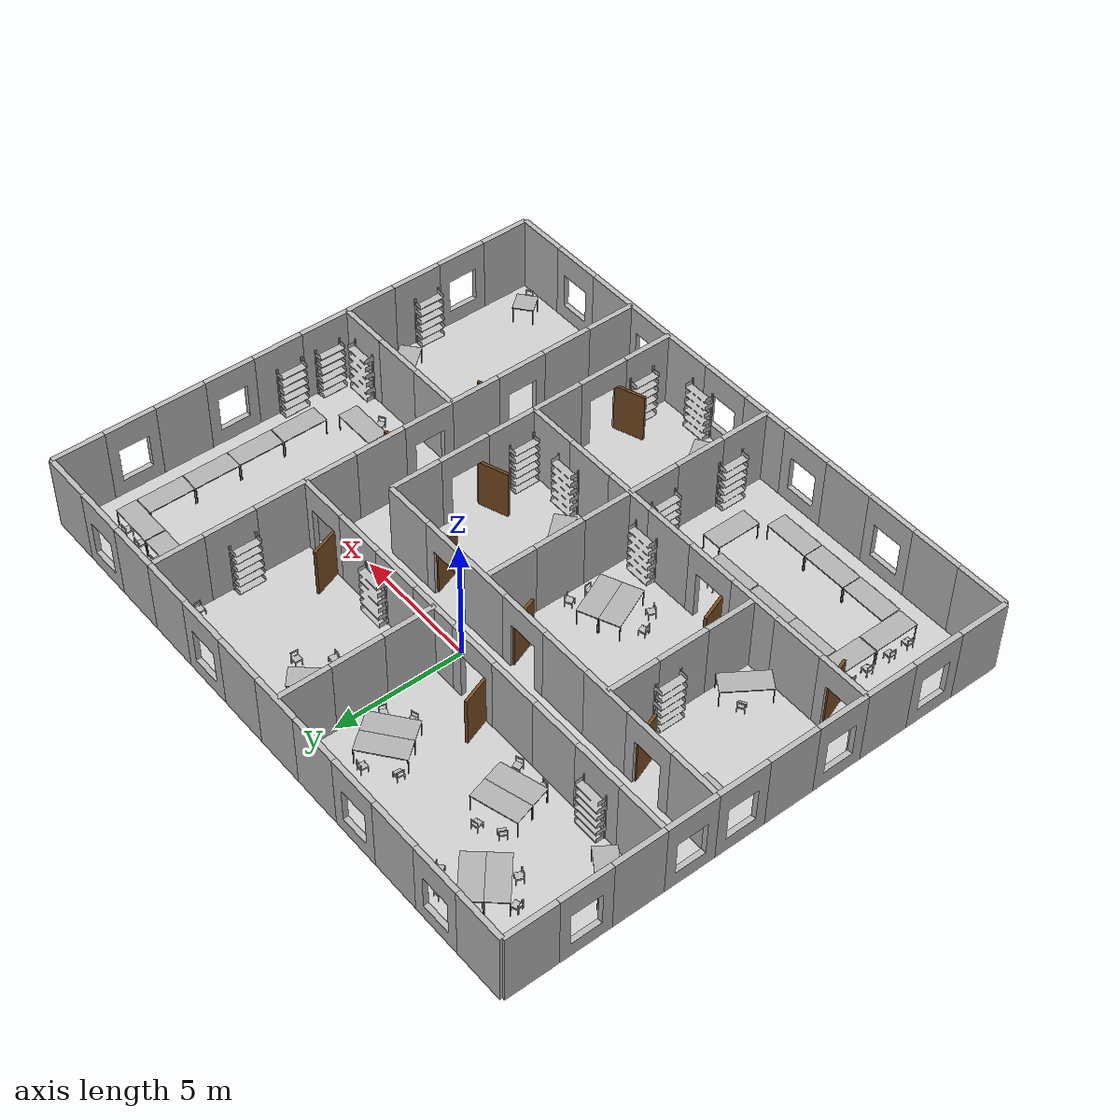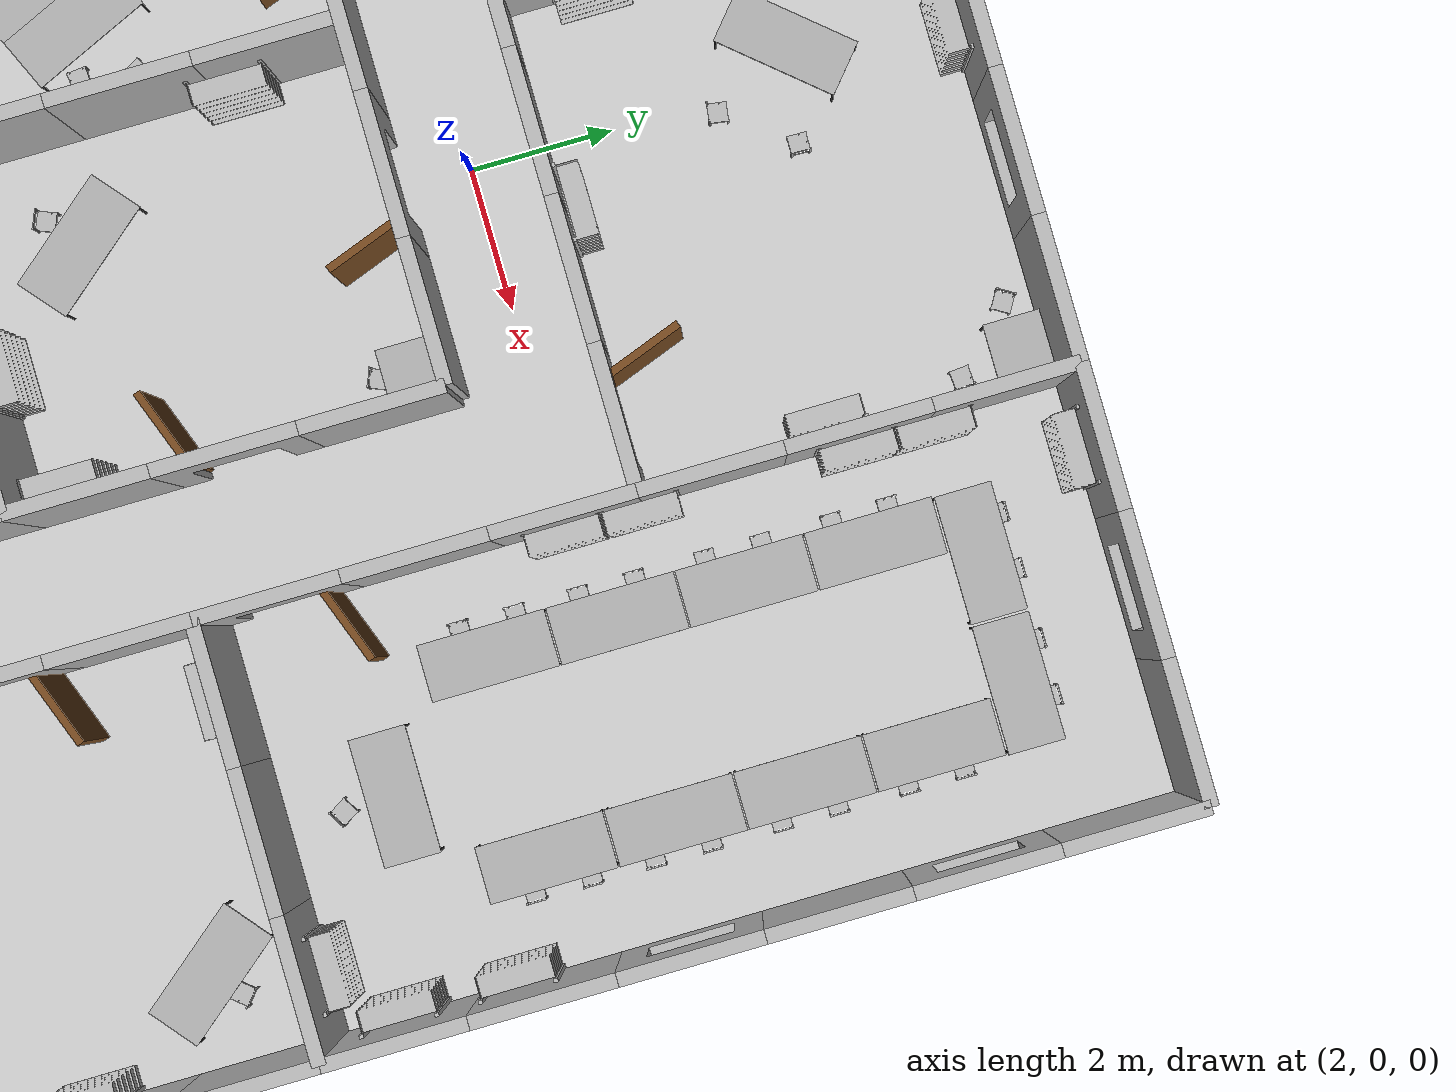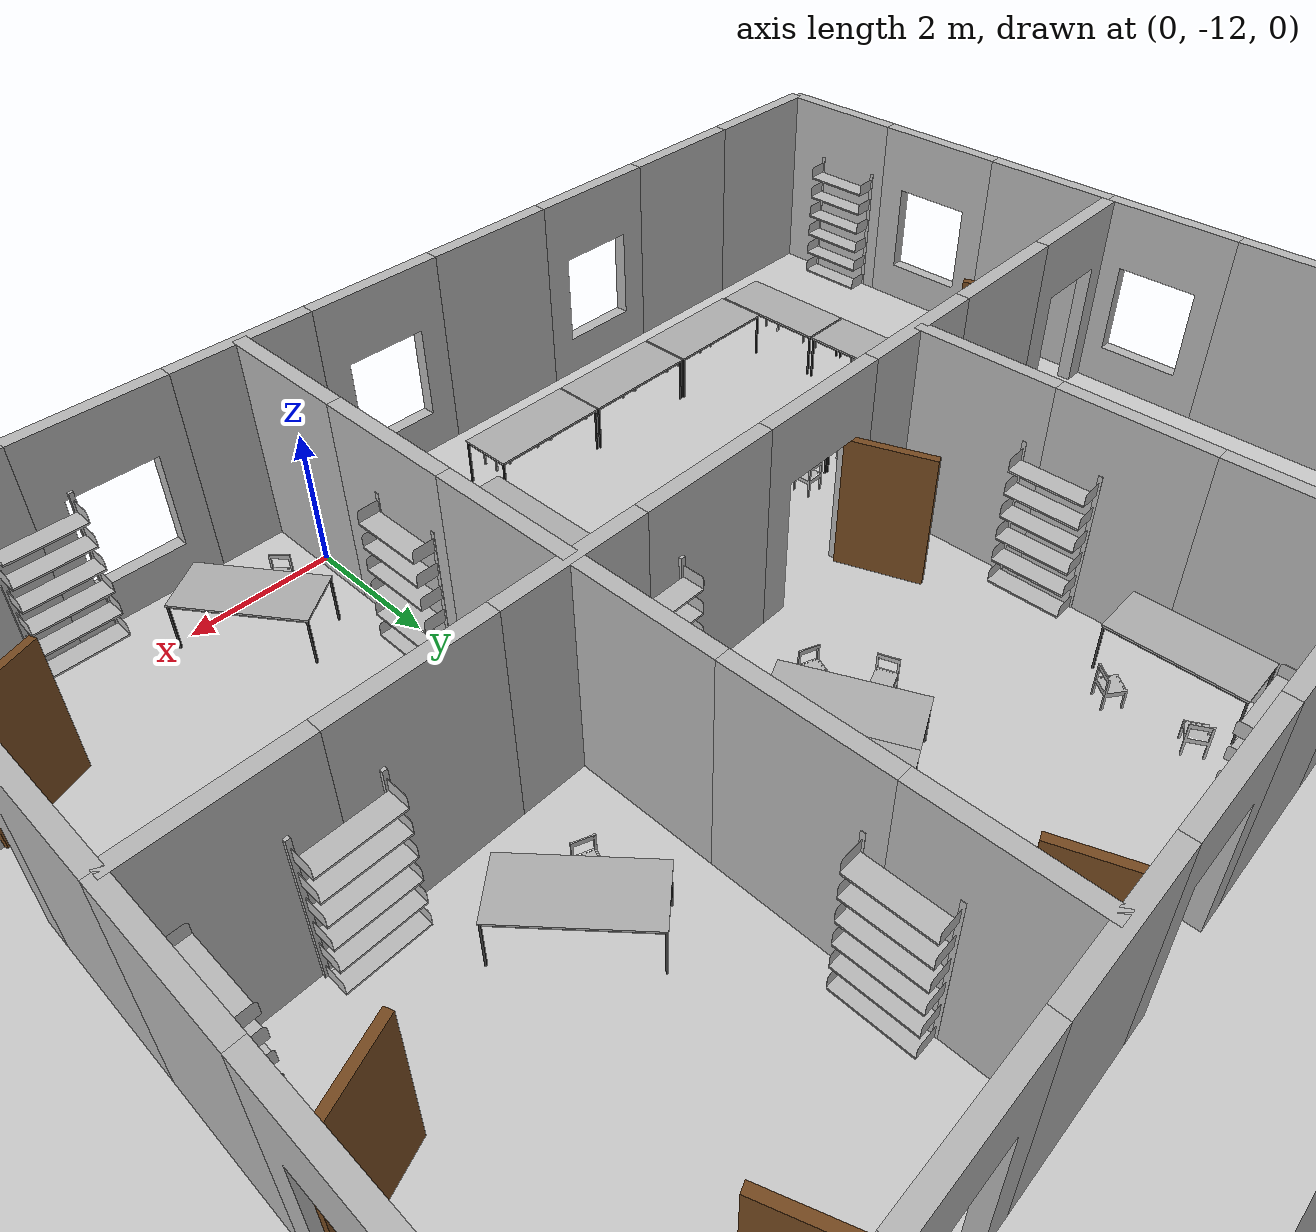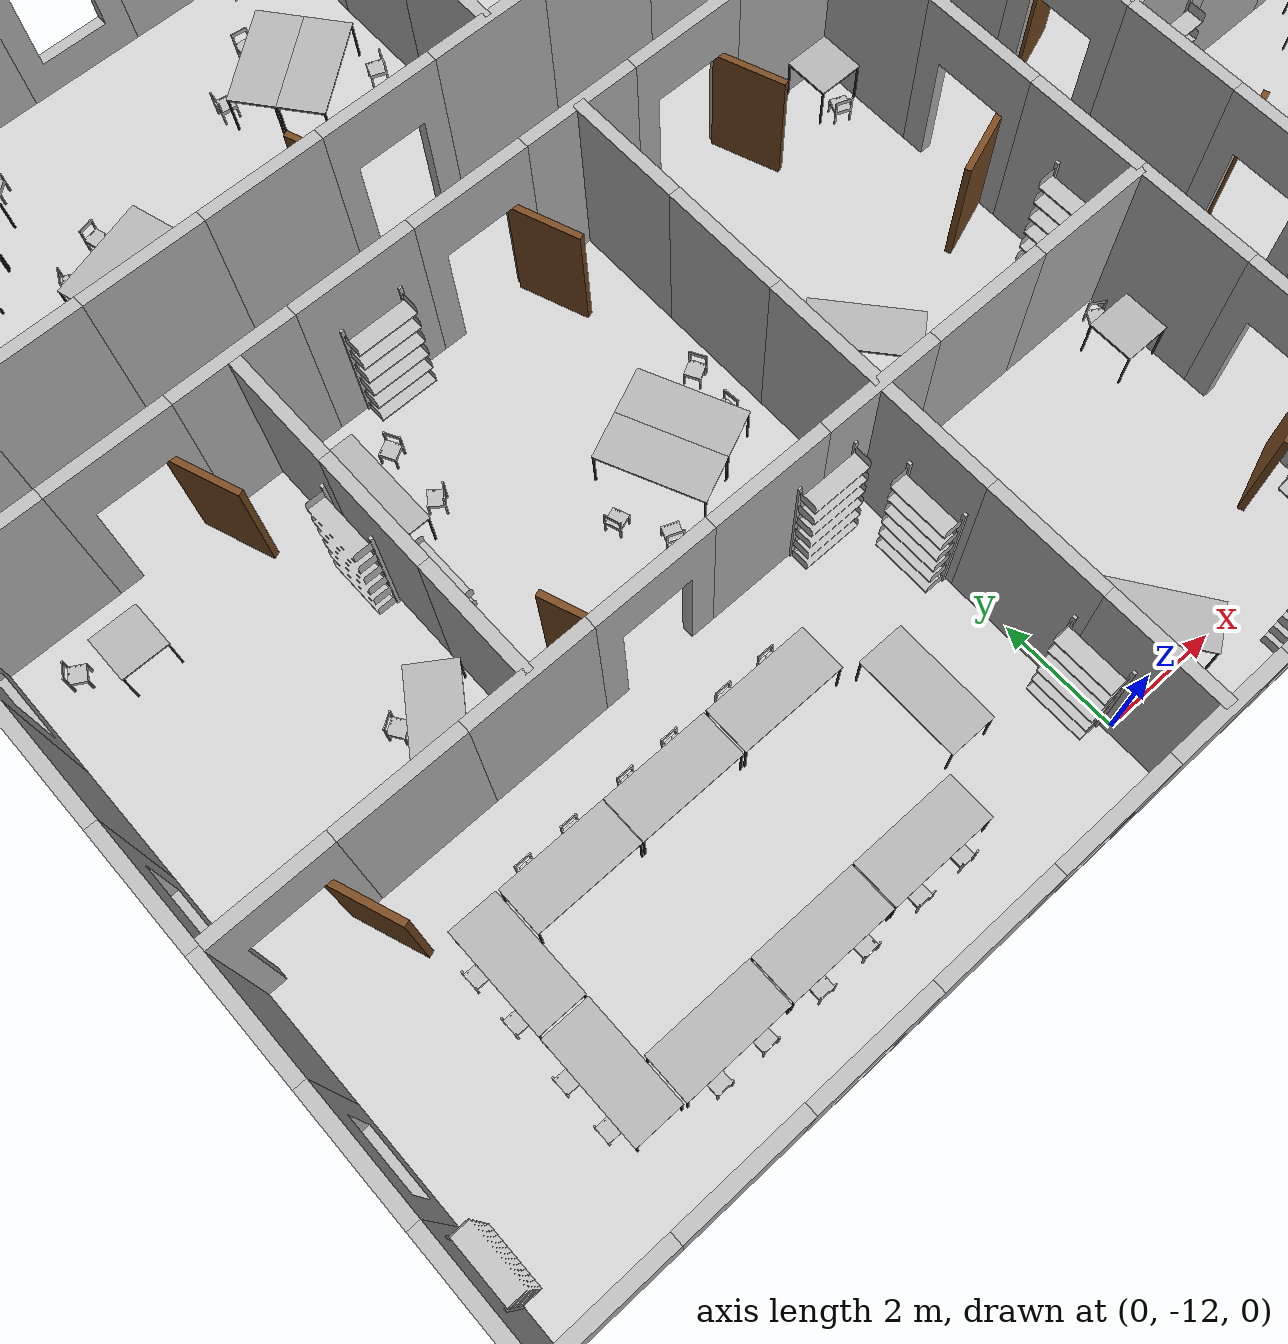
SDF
<sdf version="1.6">
 <world name="office_sim">
  <scene>
   <sky><clouds><speed>12</speed></clouds></sky>
   <ambient>0.4 0.4 0.4 1</ambient>
   <background>0.7 0.7 0.7 1</background>
   <shadows>1</shadows>
  </scene>
  <light name="sun" type="directional">
   <pose>0 0 10 0 -0 0</pose>
   <diffuse>0.8 0.8 0.8 1</diffuse>
   <specular>0.2 0.2 0.2 1</specular>
   <attenuation>
    <range>1000</range>
    <constant>0.9</constant>
    <linear>0.01</linear>
    <quadratic>0.001</quadratic>
   </attenuation>
   <direction>-0.5 0.1 -0.9</direction>
  </light>
  <model name="office_floor">
   <pose>1 -3 0 0 -0 0</pose>
   <static>1</static>
   <link name="link">
    <collision name="collision">
     <geometry><plane><normal>0 0 1</normal><size>100 100</size></plane></geometry>
     <surface><friction><ode><mu>100</mu><mu2>50</mu2></ode></friction></surface>
    </collision>
    <visual name="visual">
     <cast_shadows>0</cast_shadows>
     <geometry><plane><normal>0 0 1</normal><size>24 20</size></plane></geometry>
     <material>
      <script><uri>file://Media/materials/scripts/iai-office.material</uri><name>IAI/OfficeCarpet</name></script>
     </material>
    </visual>
   </link>
  </model>
  <light name="fill_light_2" type="directional">
   <pose>10 20 10 -1 -1 0</pose>
   <diffuse>0.2 0.18 0.18 1</diffuse>
   <specular>0.0980392 0.0980392 0.0980392 1</specular>
   <direction>0.1 0.1 -0.9</direction>
   <attenuation>
    <range>20</range>
    <constant>0.5</constant>
    <linear>0.01</linear>
    <quadratic>0.001</quadratic>
   </attenuation>
  </light>
  <light name="fill_light_0" type="directional">
   <pose>-10 -20 10 1 1 0</pose>
   <diffuse>0.25 0.2 0.2 1</diffuse>
   <specular>0.0980392 0.0980392 0.0980392 1</specular>
   <direction>0.1 0.1 -0.9</direction>
   <attenuation>
    <range>20</range>
    <constant>0.5</constant>
    <linear>0.01</linear>
    <quadratic>0.001</quadratic>
   </attenuation>
  </light>
  <model name="Shelves.031">
   <static>1</static>
   <link name="Shelves">
    <collision name="collision">
     <geometry><mesh><uri>model://Shelves/Shelves.dae</uri></mesh></geometry>
    </collision>
    <visual name="vis">
     <cast_shadows>0</cast_shadows>
     <geometry><mesh><uri>model://Shelves/Shelves.dae</uri></mesh></geometry>
    </visual>
   </link>
   <pose>-3.96844 -1.13507 0 0 -0 0</pose>
  </model>
  <model name="Shelves.030">
   <static>1</static>
   <link name="Shelves">
    <collision name="collision">
     <geometry><mesh><uri>model://Shelves/Shelves.dae</uri></mesh></geometry>
    </collision>
    <visual name="vis">
     <cast_shadows>0</cast_shadows>
     <geometry><mesh><uri>model://Shelves/Shelves.dae</uri></mesh></geometry>
    </visual>
   </link>
   <pose>-0.968436 -7.13507 0 0 -0 0</pose>
  </model>
  <model name="Shelves.029">
   <static>1</static>
   <link name="Shelves">
    <collision name="collision">
     <geometry><mesh><uri>model://Shelves/Shelves.dae</uri></mesh></geometry>
    </collision>
    <visual name="vis">
     <cast_shadows>0</cast_shadows>
     <geometry><mesh><uri>model://Shelves/Shelves.dae</uri></mesh></geometry>
    </visual>
   </link>
   <pose>8.03156 -5.13507 0 0 -0 0</pose>
  </model>
  <model name="Shelves.028">
   <static>1</static>
   <link name="Shelves">
    <collision name="collision">
     <geometry><mesh><uri>model://Shelves/Shelves.dae</uri></mesh></geometry>
    </collision>
    <visual name="vis">
     <cast_shadows>0</cast_shadows>
     <geometry><mesh><uri>model://Shelves/Shelves.dae</uri></mesh></geometry>
    </visual>
   </link>
   <pose>8.03156 6.86493 0 0 -0 0</pose>
  </model>
  <model name="Shelves.027">
   <static>1</static>
   <link name="Shelves">
    <collision name="collision">
     <geometry><mesh><uri>model://Shelves/Shelves.dae</uri></mesh></geometry>
    </collision>
    <visual name="vis">
     <cast_shadows>0</cast_shadows>
     <geometry><mesh><uri>model://Shelves/Shelves.dae</uri></mesh></geometry>
    </visual>
   </link>
   <pose>2.03156 6.86493 0 0 -0 0</pose>
  </model>
  <model name="Shelves.026">
   <static>1</static>
   <link name="Shelves">
    <collision name="collision">
     <geometry><mesh><uri>model://Shelves/Shelves.dae</uri></mesh></geometry>
    </collision>
    <visual name="vis">
     <cast_shadows>0</cast_shadows>
     <geometry><mesh><uri>model://Shelves/Shelves.dae</uri></mesh></geometry>
    </visual>
   </link>
   <pose>3.03156 1.14421 0 0 -0 -3.14159</pose>
  </model>
  <model name="Shelves.025">
   <static>1</static>
   <link name="Shelves">
    <collision name="collision">
     <geometry><mesh><uri>model://Shelves/Shelves.dae</uri></mesh></geometry>
    </collision>
    <visual name="vis">
     <cast_shadows>0</cast_shadows>
     <geometry><mesh><uri>model://Shelves/Shelves.dae</uri></mesh></geometry>
    </visual>
   </link>
   <pose>-7.96844 1.14421 0 0 -0 -3.14159</pose>
  </model>
  <model name="Shelves.024">
   <static>1</static>
   <link name="Shelves">
    <collision name="collision">
     <geometry><mesh><uri>model://Shelves/Shelves.dae</uri></mesh></geometry>
    </collision>
    <visual name="vis">
     <cast_shadows>0</cast_shadows>
     <geometry><mesh><uri>model://Shelves/Shelves.dae</uri></mesh></geometry>
    </visual>
   </link>
   <pose>-0.968436 -6.85579 0 0 -0 -3.14159</pose>
  </model>
  <model name="Shelves.023">
   <static>1</static>
   <link name="Shelves">
    <collision name="collision">
     <geometry><mesh><uri>model://Shelves/Shelves.dae</uri></mesh></geometry>
    </collision>
    <visual name="vis">
     <cast_shadows>0</cast_shadows>
     <geometry><mesh><uri>model://Shelves/Shelves.dae</uri></mesh></geometry>
    </visual>
   </link>
   <pose>11.9316 -4.8423 0 0 -0 -3.14159</pose>
  </model>
  <model name="Shelves.021">
   <static>1</static>
   <link name="Shelves">
    <collision name="collision">
     <geometry><mesh><uri>model://Shelves/Shelves.dae</uri></mesh></geometry>
    </collision>
    <visual name="vis">
     <cast_shadows>0</cast_shadows>
     <geometry><mesh><uri>model://Shelves/Shelves.dae</uri></mesh></geometry>
    </visual>
   </link>
   <pose>3.03156 -6.85579 0 0 -0 -3.14159</pose>
  </model>
  <model name="Shelves.020">
   <static>1</static>
   <link name="Shelves">
    <collision name="collision">
     <geometry><mesh><uri>model://Shelves/Shelves.dae</uri></mesh></geometry>
    </collision>
    <visual name="vis">
     <cast_shadows>0</cast_shadows>
     <geometry><mesh><uri>model://Shelves/Shelves.dae</uri></mesh></geometry>
    </visual>
   </link>
   <pose>3.03156 -12.8558 0 0 -0 -3.14159</pose>
  </model>
  <model name="Shelves.019">
   <static>1</static>
   <link name="Shelves">
    <collision name="collision">
     <geometry><mesh><uri>model://Shelves/Shelves.dae</uri></mesh></geometry>
    </collision>
    <visual name="vis">
     <cast_shadows>0</cast_shadows>
     <geometry><mesh><uri>model://Shelves/Shelves.dae</uri></mesh></geometry>
    </visual>
   </link>
   <pose>4.83156 -11.6774 0 0 -0 -1.5708</pose>
  </model>
  <model name="Shelves.018">
   <static>1</static>
   <link name="Shelves">
    <collision name="collision">
     <geometry><mesh><uri>model://Shelves/Shelves.dae</uri></mesh></geometry>
    </collision>
    <visual name="vis">
     <cast_shadows>0</cast_shadows>
     <geometry><mesh><uri>model://Shelves/Shelves.dae</uri></mesh></geometry>
    </visual>
   </link>
   <pose>-0.168436 -8.34184 0 0 -0 -1.5708</pose>
  </model>
  <model name="Shelves.017">
   <static>1</static>
   <link name="Shelves">
    <collision name="collision">
     <geometry><mesh><uri>model://Shelves/Shelves.dae</uri></mesh></geometry>
    </collision>
    <visual name="vis">
     <cast_shadows>0</cast_shadows>
     <geometry><mesh><uri>model://Shelves/Shelves.dae</uri></mesh></geometry>
    </visual>
   </link>
   <pose>-0.168436 -11.3418 0 0 -0 -1.5708</pose>
  </model>
  <model name="Shelves.016">
   <static>1</static>
   <link name="Shelves">
    <collision name="collision">
     <geometry><mesh><uri>model://Shelves/Shelves.dae</uri></mesh></geometry>
    </collision>
    <visual name="vis">
     <cast_shadows>0</cast_shadows>
     <geometry><mesh><uri>model://Shelves/Shelves.dae</uri></mesh></geometry>
    </visual>
   </link>
   <pose>-6.16844 -3.34184 0 0 -0 -1.5708</pose>
  </model>
  <model name="Shelves.015">
   <static>1</static>
   <link name="Shelves">
    <collision name="collision">
     <geometry><mesh><uri>model://Shelves/Shelves.dae</uri></mesh></geometry>
    </collision>
    <visual name="vis">
     <cast_shadows>0</cast_shadows>
     <geometry><mesh><uri>model://Shelves/Shelves.dae</uri></mesh></geometry>
    </visual>
   </link>
   <pose>6.83156 3.65816 0 0 -0 -1.5708</pose>
  </model>
  <model name="Shelves.014">
   <static>1</static>
   <link name="Shelves">
    <collision name="collision">
     <geometry><mesh><uri>model://Shelves/Shelves.dae</uri></mesh></geometry>
    </collision>
    <visual name="vis">
     <cast_shadows>0</cast_shadows>
     <geometry><mesh><uri>model://Shelves/Shelves.dae</uri></mesh></geometry>
    </visual>
   </link>
   <pose>4.83156 -6.34184 0 0 -0 -1.5708</pose>
  </model>
  <model name="Shelves.013">
   <static>1</static>
   <link name="Shelves">
    <collision name="collision">
     <geometry><mesh><uri>model://Shelves/Shelves.dae</uri></mesh></geometry>
    </collision>
    <visual name="vis">
     <cast_shadows>0</cast_shadows>
     <geometry><mesh><uri>model://Shelves/Shelves.dae</uri></mesh></geometry>
    </visual>
   </link>
   <pose>12.8316 -8.34184 0 0 -0 -1.5708</pose>
  </model>
  <model name="Shelves.012">
   <static>1</static>
   <link name="Shelves">
    <collision name="collision">
     <geometry><mesh><uri>model://Shelves/Shelves.dae</uri></mesh></geometry>
    </collision>
    <visual name="vis">
     <cast_shadows>0</cast_shadows>
     <geometry><mesh><uri>model://Shelves/Shelves.dae</uri></mesh></geometry>
    </visual>
   </link>
   <pose>12.8316 -2.34184 0 0 -0 -1.5708</pose>
  </model>
  <model name="Shelves.011">
   <static>1</static>
   <link name="Shelves">
    <collision name="collision">
     <geometry><mesh><uri>model://Shelves/Shelves.dae</uri></mesh></geometry>
    </collision>
    <visual name="vis">
     <cast_shadows>0</cast_shadows>
     <geometry><mesh><uri>model://Shelves/Shelves.dae</uri></mesh></geometry>
    </visual>
   </link>
   <pose>12.8316 -3.97036 0 0 -0 -1.5708</pose>
  </model>
  <model name="Shelves.010">
   <static>1</static>
   <link name="Shelves">
    <collision name="collision">
     <geometry><mesh><uri>model://Shelves/Shelves.dae</uri></mesh></geometry>
    </collision>
    <visual name="vis">
     <cast_shadows>0</cast_shadows>
     <geometry><mesh><uri>model://Shelves/Shelves.dae</uri></mesh></geometry>
    </visual>
   </link>
   <pose>-5.89665 -4.74184 0 0 -0 1.5708</pose>
  </model>
  <model name="Shelves.009">
   <static>1</static>
   <link name="Shelves">
    <collision name="collision">
     <geometry><mesh><uri>model://Shelves/Shelves.dae</uri></mesh></geometry>
    </collision>
    <visual name="vis">
     <cast_shadows>0</cast_shadows>
     <geometry><mesh><uri>model://Shelves/Shelves.dae</uri></mesh></geometry>
    </visual>
   </link>
   <pose>7.10335 -9.7003 0 0 -0 1.5708</pose>
  </model>
  <model name="Shelves.008">
   <static>1</static>
   <link name="Shelves">
    <collision name="collision">
     <geometry><mesh><uri>model://Shelves/Shelves.dae</uri></mesh></geometry>
    </collision>
    <visual name="vis">
     <cast_shadows>0</cast_shadows>
     <geometry><mesh><uri>model://Shelves/Shelves.dae</uri></mesh></geometry>
    </visual>
   </link>
   <pose>-10.8966 -11.7418 0 0 -0 1.5708</pose>
  </model>
  <model name="Shelves.007">
   <static>1</static>
   <link name="Shelves">
    <collision name="collision">
     <geometry><mesh><uri>model://Shelves/Shelves.dae</uri></mesh></geometry>
    </collision>
    <visual name="vis">
     <cast_shadows>0</cast_shadows>
     <geometry><mesh><uri>model://Shelves/Shelves.dae</uri></mesh></geometry>
    </visual>
   </link>
   <pose>0.103355 -9.74184 0 0 -0 1.5708</pose>
  </model>
  <model name="Shelves.006">
   <static>1</static>
   <link name="Shelves">
    <collision name="collision">
     <geometry><mesh><uri>model://Shelves/Shelves.dae</uri></mesh></geometry>
    </collision>
    <visual name="vis">
     <cast_shadows>0</cast_shadows>
     <geometry><mesh><uri>model://Shelves/Shelves.dae</uri></mesh></geometry>
    </visual>
   </link>
   <pose>0.103355 -2.74184 0 0 -0 1.5708</pose>
  </model>
  <model name="Shelves.005">
   <static>1</static>
   <link name="Shelves">
    <collision name="collision">
     <geometry><mesh><uri>model://Shelves/Shelves.dae</uri></mesh></geometry>
    </collision>
    <visual name="vis">
     <cast_shadows>0</cast_shadows>
     <geometry><mesh><uri>model://Shelves/Shelves.dae</uri></mesh></geometry>
    </visual>
   </link>
   <pose>0.103355 2.25816 0 0 -0 1.5708</pose>
  </model>
  <model name="Shelves.004">
   <static>1</static>
   <link name="Shelves">
    <collision name="collision">
     <geometry><mesh><uri>model://Shelves/Shelves.dae</uri></mesh></geometry>
    </collision>
    <visual name="vis">
     <cast_shadows>0</cast_shadows>
     <geometry><mesh><uri>model://Shelves/Shelves.dae</uri></mesh></geometry>
    </visual>
   </link>
   <pose>7.10335 5.0286 0 0 -0 1.5708</pose>
  </model>
  <model name="Shelves.003">
   <static>1</static>
   <link name="Shelves">
    <collision name="collision">
     <geometry><mesh><uri>model://Shelves/Shelves.dae</uri></mesh></geometry>
    </collision>
    <visual name="vis">
     <cast_shadows>0</cast_shadows>
     <geometry><mesh><uri>model://Shelves/Shelves.dae</uri></mesh></geometry>
    </visual>
   </link>
   <pose>7.10335 3.96468 0 0 -0 1.5708</pose>
  </model>
  <model name="Shelves.002">
   <static>1</static>
   <link name="Shelves">
    <collision name="collision">
     <geometry><mesh><uri>model://Shelves/Shelves.dae</uri></mesh></geometry>
    </collision>
    <visual name="vis">
     <cast_shadows>0</cast_shadows>
     <geometry><mesh><uri>model://Shelves/Shelves.dae</uri></mesh></geometry>
    </visual>
   </link>
   <pose>7.10335 0.964682 0 0 -0 1.5708</pose>
  </model>
  <model name="Shelves.001">
   <static>1</static>
   <link name="Shelves">
    <collision name="collision">
     <geometry><mesh><uri>model://Shelves/Shelves.dae</uri></mesh></geometry>
    </collision>
    <visual name="vis">
     <cast_shadows>0</cast_shadows>
     <geometry><mesh><uri>model://Shelves/Shelves.dae</uri></mesh></geometry>
    </visual>
   </link>
   <pose>7.10335 -0.11143 0 0 -0 1.5708</pose>
  </model>
  <model name="DoorOpen.011">
   <static>1</static>
   <link name="DoorOpen">
    <collision name="collision">
     <geometry><mesh><uri>model://DoorOpen/DoorOpen.dae</uri></mesh></geometry>
    </collision>
    <visual name="vis">
     <cast_shadows>0</cast_shadows>
     <geometry><mesh><uri>model://DoorOpen/DoorOpen.dae</uri></mesh></geometry>
    </visual>
   </link>
   <pose>-2 1 0 0 -0 0</pose>
  </model>
  <model name="DoorOpen.010">
   <static>1</static>
   <link name="DoorOpen">
    <collision name="collision">
     <geometry><mesh><uri>model://DoorOpen/DoorOpen.dae</uri></mesh></geometry>
    </collision>
    <visual name="vis">
     <cast_shadows>0</cast_shadows>
     <geometry><mesh><uri>model://DoorOpen/DoorOpen.dae</uri></mesh></geometry>
    </visual>
   </link>
   <pose>6 1 0 0 -0 0</pose>
  </model>
  <model name="DoorOpen.009">
   <static>1</static>
   <link name="DoorOpen">
    <collision name="collision">
     <geometry><mesh><uri>model://DoorOpen/DoorOpen.dae</uri></mesh></geometry>
    </collision>
    <visual name="vis">
     <cast_shadows>0</cast_shadows>
     <geometry><mesh><uri>model://DoorOpen/DoorOpen.dae</uri></mesh></geometry>
    </visual>
   </link>
   <pose>-2 -1 0 0 -0 3.14159</pose>
  </model>
  <model name="DoorOpen.008">
   <static>1</static>
   <link name="DoorOpen">
    <collision name="collision">
     <geometry><mesh><uri>model://DoorOpen/DoorOpen.dae</uri></mesh></geometry>
    </collision>
    <visual name="vis">
     <cast_shadows>0</cast_shadows>
     <geometry><mesh><uri>model://DoorOpen/DoorOpen.dae</uri></mesh></geometry>
    </visual>
   </link>
   <pose>-10 -7 0 0 -0 3.14159</pose>
  </model>
  <model name="DoorOpen.007">
   <static>1</static>
   <link name="DoorOpen">
    <collision name="collision">
     <geometry><mesh><uri>model://DoorOpen/DoorOpen.dae</uri></mesh></geometry>
    </collision>
    <visual name="vis">
     <cast_shadows>0</cast_shadows>
     <geometry><mesh><uri>model://DoorOpen/DoorOpen.dae</uri></mesh></geometry>
    </visual>
   </link>
   <pose>-8 -1 0 0 -0 3.14159</pose>
  </model>
  <model name="DoorOpen.006">
   <static>1</static>
   <link name="DoorOpen">
    <collision name="collision">
     <geometry><mesh><uri>model://DoorOpen/DoorOpen.dae</uri></mesh></geometry>
    </collision>
    <visual name="vis">
     <cast_shadows>0</cast_shadows>
     <geometry><mesh><uri>model://DoorOpen/DoorOpen.dae</uri></mesh></geometry>
    </visual>
   </link>
   <pose>2 -1 0 0 -0 3.14159</pose>
  </model>
  <model name="DoorOpen.005">
   <static>1</static>
   <link name="DoorOpen">
    <collision name="collision">
     <geometry><mesh><uri>model://DoorOpen/DoorOpen.dae</uri></mesh></geometry>
    </collision>
    <visual name="vis">
     <cast_shadows>0</cast_shadows>
     <geometry><mesh><uri>model://DoorOpen/DoorOpen.dae</uri></mesh></geometry>
    </visual>
   </link>
   <pose>5 -10 0 0 -0 1.5708</pose>
  </model>
  <model name="DoorOpen.004">
   <static>1</static>
   <link name="DoorOpen">
    <collision name="collision">
     <geometry><mesh><uri>model://DoorOpen/DoorOpen.dae</uri></mesh></geometry>
    </collision>
    <visual name="vis">
     <cast_shadows>0</cast_shadows>
     <geometry><mesh><uri>model://DoorOpen/DoorOpen.dae</uri></mesh></geometry>
    </visual>
   </link>
   <pose>5 -4 0 0 -0 1.5708</pose>
  </model>
  <model name="DoorOpen.003">
   <static>1</static>
   <link name="DoorOpen">
    <collision name="collision">
     <geometry><mesh><uri>model://DoorOpen/DoorOpen.dae</uri></mesh></geometry>
    </collision>
    <visual name="vis">
     <cast_shadows>0</cast_shadows>
     <geometry><mesh><uri>model://DoorOpen/DoorOpen.dae</uri></mesh></geometry>
    </visual>
   </link>
   <pose>7 -4 0 0 0 -1.5708</pose>
  </model>
  <model name="DoorOpen.002">
   <static>1</static>
   <link name="DoorOpen">
    <collision name="collision">
     <geometry><mesh><uri>model://DoorOpen/DoorOpen.dae</uri></mesh></geometry>
    </collision>
    <visual name="vis">
     <cast_shadows>0</cast_shadows>
     <geometry><mesh><uri>model://DoorOpen/DoorOpen.dae</uri></mesh></geometry>
    </visual>
   </link>
   <pose>7 -8 0 0 0 -1.5708</pose>
  </model>
  <model name="DoorOpen.001">
   <static>1</static>
   <link name="DoorOpen">
    <collision name="collision">
     <geometry><mesh><uri>model://DoorOpen/DoorOpen.dae</uri></mesh></geometry>
    </collision>
    <visual name="vis">
     <cast_shadows>0</cast_shadows>
     <geometry><mesh><uri>model://DoorOpen/DoorOpen.dae</uri></mesh></geometry>
    </visual>
   </link>
   <pose>-4 -7 0 0 -0 0</pose>
  </model>
  <model name="chair.077">
   <static>1</static>
   <link name="Chair">
    <collision name="collision"><geometry><mesh><uri>model://Chair/Chair.dae</uri></mesh></geometry></collision>
    <visual name="vis">
     <cast_shadows>0</cast_shadows>
     <geometry><mesh><uri>model://Chair/Chair.dae</uri></mesh></geometry>
    </visual>
   </link>
   <pose>-1.17679 6.46121 0 0 -0 1.05807</pose>
  </model>
  <model name="chair.076">
   <static>1</static>
   <link name="Chair">
    <collision name="collision"><geometry><mesh><uri>model://Chair/Chair.dae</uri></mesh></geometry></collision>
    <visual name="vis">
     <cast_shadows>0</cast_shadows>
     <geometry><mesh><uri>model://Chair/Chair.dae</uri></mesh></geometry>
    </visual>
   </link>
   <pose>-9.85611 6.46121 0 0 0 -0.949062</pose>
  </model>
  <model name="chair.075">
   <static>1</static>
   <link name="Chair">
    <collision name="collision"><geometry><mesh><uri>model://Chair/Chair.dae</uri></mesh></geometry></collision>
    <visual name="vis">
     <cast_shadows>0</cast_shadows>
     <geometry><mesh><uri>model://Chair/Chair.dae</uri></mesh></geometry>
    </visual>
   </link>
   <pose>-10.422 5.51803 0 0 -0 2.39536</pose>
  </model>
  <model name="chair.074">
   <static>1</static>
   <link name="Chair">
    <collision name="collision"><geometry><mesh><uri>model://Chair/Chair.dae</uri></mesh></geometry></collision>
    <visual name="vis">
     <cast_shadows>0</cast_shadows>
     <geometry><mesh><uri>model://Chair/Chair.dae</uri></mesh></geometry>
    </visual>
   </link>
   <pose>-10.422 1.51803 0 0 -0 2.39536</pose>
  </model>
  <model name="chair.073">
   <static>1</static>
   <link name="Chair">
    <collision name="collision"><geometry><mesh><uri>model://Chair/Chair.dae</uri></mesh></geometry></collision>
    <visual name="vis">
     <cast_shadows>0</cast_shadows>
     <geometry><mesh><uri>model://Chair/Chair.dae</uri></mesh></geometry>
    </visual>
   </link>
   <pose>-8.89406 4.80098 0 0 -0 1.91933</pose>
  </model>
  <model name="chair.072">
   <static>1</static>
   <link name="Chair">
    <collision name="collision"><geometry><mesh><uri>model://Chair/Chair.dae</uri></mesh></geometry></collision>
    <visual name="vis">
     <cast_shadows>0</cast_shadows>
     <geometry><mesh><uri>model://Chair/Chair.dae</uri></mesh></geometry>
    </visual>
   </link>
   <pose>-8.12065 4.10302 0 0 -0 2.75264</pose>
  </model>
  <model name="chair.071">
   <static>1</static>
   <link name="Chair">
    <collision name="collision"><geometry><mesh><uri>model://Chair/Chair.dae</uri></mesh></geometry></collision>
    <visual name="vis">
     <cast_shadows>0</cast_shadows>
     <geometry><mesh><uri>model://Chair/Chair.dae</uri></mesh></geometry>
    </visual>
   </link>
   <pose>-7.11295 6.28751 0 0 0 -0.039891</pose>
  </model>
  <model name="chair.070">
   <static>1</static>
   <link name="Chair">
    <collision name="collision"><geometry><mesh><uri>model://Chair/Chair.dae</uri></mesh></geometry></collision>
    <visual name="vis">
     <cast_shadows>0</cast_shadows>
     <geometry><mesh><uri>model://Chair/Chair.dae</uri></mesh></geometry>
    </visual>
   </link>
   <pose>-6.44881 5.78649 0 0 0 -0.873194</pose>
  </model>
  <model name="chair.069">
   <static>1</static>
   <link name="Chair">
    <collision name="collision"><geometry><mesh><uri>model://Chair/Chair.dae</uri></mesh></geometry></collision>
    <visual name="vis">
     <cast_shadows>0</cast_shadows>
     <geometry><mesh><uri>model://Chair/Chair.dae</uri></mesh></geometry>
    </visual>
   </link>
   <pose>-4.85922 1.56113 0 0 0 -2.73033</pose>
  </model>
  <model name="chair.068">
   <static>1</static>
   <link name="Chair">
    <collision name="collision"><geometry><mesh><uri>model://Chair/Chair.dae</uri></mesh></geometry></collision>
    <visual name="vis">
     <cast_shadows>0</cast_shadows>
     <geometry><mesh><uri>model://Chair/Chair.dae</uri></mesh></geometry>
    </visual>
   </link>
   <pose>-5.95773 1.50503 0 0 -0 2.92372</pose>
  </model>
  <model name="chair.067">
   <static>1</static>
   <link name="Chair">
    <collision name="collision"><geometry><mesh><uri>model://Chair/Chair.dae</uri></mesh></geometry></collision>
    <visual name="vis">
     <cast_shadows>0</cast_shadows>
     <geometry><mesh><uri>model://Chair/Chair.dae</uri></mesh></geometry>
    </visual>
   </link>
   <pose>-5.81634 3.89299 0 0 -0 0.26127</pose>
  </model>
  <model name="chair.066">
   <static>1</static>
   <link name="Chair">
    <collision name="collision"><geometry><mesh><uri>model://Chair/Chair.dae</uri></mesh></geometry></collision>
    <visual name="vis">
     <cast_shadows>0</cast_shadows>
     <geometry><mesh><uri>model://Chair/Chair.dae</uri></mesh></geometry>
    </visual>
   </link>
   <pose>-6.5511 3.50282 0 0 -0 1.09457</pose>
  </model>
  <model name="chair.065">
   <static>1</static>
   <link name="Chair">
    <collision name="collision"><geometry><mesh><uri>model://Chair/Chair.dae</uri></mesh></geometry></collision>
    <visual name="vis">
     <cast_shadows>0</cast_shadows>
     <geometry><mesh><uri>model://Chair/Chair.dae</uri></mesh></geometry>
    </visual>
   </link>
   <pose>-2.8286 4.61296 0 0 -0 1.44364</pose>
  </model>
  <model name="chair.064">
   <static>1</static>
   <link name="Chair">
    <collision name="collision"><geometry><mesh><uri>model://Chair/Chair.dae</uri></mesh></geometry></collision>
    <visual name="vis">
     <cast_shadows>0</cast_shadows>
     <geometry><mesh><uri>model://Chair/Chair.dae</uri></mesh></geometry>
    </visual>
   </link>
   <pose>-1.89432 5.30636 0 0 0 -0.120868</pose>
  </model>
  <model name="chair.063">
   <static>1</static>
   <link name="Chair">
    <collision name="collision"><geometry><mesh><uri>model://Chair/Chair.dae</uri></mesh></geometry></collision>
    <visual name="vis">
     <cast_shadows>0</cast_shadows>
     <geometry><mesh><uri>model://Chair/Chair.dae</uri></mesh></geometry>
    </visual>
   </link>
   <pose>-1.39274 3.00957 0 0 0 -2.79306</pose>
  </model>
  <model name="chair.062">
   <static>1</static>
   <link name="Chair">
    <collision name="collision"><geometry><mesh><uri>model://Chair/Chair.dae</uri></mesh></geometry></collision>
    <visual name="vis">
     <cast_shadows>0</cast_shadows>
     <geometry><mesh><uri>model://Chair/Chair.dae</uri></mesh></geometry>
    </visual>
   </link>
   <pose>-0.597138 3.55061 0 0 0 -1.94892</pose>
  </model>
  <model name="chair.061">
   <static>1</static>
   <link name="Chair">
    <collision name="collision"><geometry><mesh><uri>model://Chair/Chair.dae</uri></mesh></geometry></collision>
    <visual name="vis">
     <cast_shadows>0</cast_shadows>
     <geometry><mesh><uri>model://Chair/Chair.dae</uri></mesh></geometry>
    </visual>
   </link>
   <pose>5.78957 6.49669 0 0 -0 1.02957</pose>
  </model>
  <model name="chair.060">
   <static>1</static>
   <link name="Chair">
    <collision name="collision"><geometry><mesh><uri>model://Chair/Chair.dae</uri></mesh></geometry></collision>
    <visual name="vis">
     <cast_shadows>0</cast_shadows>
     <geometry><mesh><uri>model://Chair/Chair.dae</uri></mesh></geometry>
    </visual>
   </link>
   <pose>6.63843 5.66354 0 0 0 -1.49217</pose>
  </model>
  <model name="chair.059">
   <static>1</static>
   <link name="Chair">
    <collision name="collision"><geometry><mesh><uri>model://Chair/Chair.dae</uri></mesh></geometry></collision>
    <visual name="vis">
     <cast_shadows>0</cast_shadows>
     <geometry><mesh><uri>model://Chair/Chair.dae</uri></mesh></geometry>
    </visual>
   </link>
   <pose>2.20546 3.46278 0 0 -0 3.01177</pose>
  </model>
  <model name="chair.058">
   <static>1</static>
   <link name="Chair">
    <collision name="collision"><geometry><mesh><uri>model://Chair/Chair.dae</uri></mesh></geometry></collision>
    <visual name="vis">
     <cast_shadows>0</cast_shadows>
     <geometry><mesh><uri>model://Chair/Chair.dae</uri></mesh></geometry>
    </visual>
   </link>
   <pose>2.92595 4.41251 0 0 0 -1.59587</pose>
  </model>
  <model name="chair.057">
   <static>1</static>
   <link name="Chair">
    <collision name="collision"><geometry><mesh><uri>model://Chair/Chair.dae</uri></mesh></geometry></collision>
    <visual name="vis">
     <cast_shadows>0</cast_shadows>
     <geometry><mesh><uri>model://Chair/Chair.dae</uri></mesh></geometry>
    </visual>
   </link>
   <pose>0.447908 4.96925 0 0 -0 1.10939</pose>
  </model>
  <model name="chair.056">
   <static>1</static>
   <link name="Chair">
    <collision name="collision"><geometry><mesh><uri>model://Chair/Chair.dae</uri></mesh></geometry></collision>
    <visual name="vis">
     <cast_shadows>0</cast_shadows>
     <geometry><mesh><uri>model://Chair/Chair.dae</uri></mesh></geometry>
    </visual>
   </link>
   <pose>-10.1681 -1.84678 0 0 -0 1.03445</pose>
  </model>
  <model name="chair.055">
   <static>1</static>
   <link name="Chair">
    <collision name="collision"><geometry><mesh><uri>model://Chair/Chair.dae</uri></mesh></geometry></collision>
    <visual name="vis">
     <cast_shadows>0</cast_shadows>
     <geometry><mesh><uri>model://Chair/Chair.dae</uri></mesh></geometry>
    </visual>
   </link>
   <pose>-7.35992 -5.45733 0 0 -0 0.598117</pose>
  </model>
  <model name="chair.054">
   <static>1</static>
   <link name="Chair">
    <collision name="collision"><geometry><mesh><uri>model://Chair/Chair.dae</uri></mesh></geometry></collision>
    <visual name="vis">
     <cast_shadows>0</cast_shadows>
     <geometry><mesh><uri>model://Chair/Chair.dae</uri></mesh></geometry>
    </visual>
   </link>
   <pose>-4.7587 -3.08711 0 0 0 -2.22892</pose>
  </model>
  <model name="chair.053">
   <static>1</static>
   <link name="Chair">
    <collision name="collision"><geometry><mesh><uri>model://Chair/Chair.dae</uri></mesh></geometry></collision>
    <visual name="vis">
     <cast_shadows>0</cast_shadows>
     <geometry><mesh><uri>model://Chair/Chair.dae</uri></mesh></geometry>
    </visual>
   </link>
   <pose>-4.7587 -2.03075 0 0 0 -1.07227</pose>
  </model>
  <model name="chair.051">
   <static>1</static>
   <link name="Chair">
    <collision name="collision"><geometry><mesh><uri>model://Chair/Chair.dae</uri></mesh></geometry></collision>
    <visual name="vis">
     <cast_shadows>0</cast_shadows>
     <geometry><mesh><uri>model://Chair/Chair.dae</uri></mesh></geometry>
    </visual>
   </link>
   <pose>-0.552092 -4.03075 0 0 0 -1.07227</pose>
  </model>
  <model name="chair.050">
   <static>1</static>
   <link name="Chair">
    <collision name="collision"><geometry><mesh><uri>model://Chair/Chair.dae</uri></mesh></geometry></collision>
    <visual name="vis">
     <cast_shadows>0</cast_shadows>
     <geometry><mesh><uri>model://Chair/Chair.dae</uri></mesh></geometry>
    </visual>
   </link>
   <pose>-0.672709 -4.8221 0 0 0 -1.48406</pose>
  </model>
  <model name="chair.049">
   <static>1</static>
   <link name="Chair">
    <collision name="collision"><geometry><mesh><uri>model://Chair/Chair.dae</uri></mesh></geometry></collision>
    <visual name="vis">
     <cast_shadows>0</cast_shadows>
     <geometry><mesh><uri>model://Chair/Chair.dae</uri></mesh></geometry>
    </visual>
   </link>
   <pose>-3.04582 -5.09608 0 0 -0 1.91933</pose>
  </model>
  <model name="chair.048">
   <static>1</static>
   <link name="Chair">
    <collision name="collision"><geometry><mesh><uri>model://Chair/Chair.dae</uri></mesh></geometry></collision>
    <visual name="vis">
     <cast_shadows>0</cast_shadows>
     <geometry><mesh><uri>model://Chair/Chair.dae</uri></mesh></geometry>
    </visual>
   </link>
   <pose>1.08533 -5.79404 0 0 -0 2.75264</pose>
  </model>
  <model name="chair.047">
   <static>1</static>
   <link name="Chair">
    <collision name="collision"><geometry><mesh><uri>model://Chair/Chair.dae</uri></mesh></geometry></collision>
    <visual name="vis">
     <cast_shadows>0</cast_shadows>
     <geometry><mesh><uri>model://Chair/Chair.dae</uri></mesh></geometry>
    </visual>
   </link>
   <pose>7.59996 -11.3455 0 0 -0 1.20669</pose>
  </model>
  <model name="chair.046">
   <static>1</static>
   <link name="Chair">
    <collision name="collision"><geometry><mesh><uri>model://Chair/Chair.dae</uri></mesh></geometry></collision>
    <visual name="vis">
     <cast_shadows>0</cast_shadows>
     <geometry><mesh><uri>model://Chair/Chair.dae</uri></mesh></geometry>
    </visual>
   </link>
   <pose>8.05269 -12.3867 0 0 -0 2.24947</pose>
  </model>
  <model name="chair.045">
   <static>1</static>
   <link name="Chair">
    <collision name="collision"><geometry><mesh><uri>model://Chair/Chair.dae</uri></mesh></geometry></collision>
    <visual name="vis">
     <cast_shadows>0</cast_shadows>
     <geometry><mesh><uri>model://Chair/Chair.dae</uri></mesh></geometry>
    </visual>
   </link>
   <pose>9.05269 -12.3867 0 0 0 -2.59411</pose>
  </model>
  <model name="chair.044">
   <static>1</static>
   <link name="Chair">
    <collision name="collision"><geometry><mesh><uri>model://Chair/Chair.dae</uri></mesh></geometry></collision>
    <visual name="vis">
     <cast_shadows>0</cast_shadows>
     <geometry><mesh><uri>model://Chair/Chair.dae</uri></mesh></geometry>
    </visual>
   </link>
   <pose>4.43473 -2.00327 0 0 -0 2.75264</pose>
  </model>
  <model name="chair.043">
   <static>1</static>
   <link name="Chair">
    <collision name="collision"><geometry><mesh><uri>model://Chair/Chair.dae</uri></mesh></geometry></collision>
    <visual name="vis">
     <cast_shadows>0</cast_shadows>
     <geometry><mesh><uri>model://Chair/Chair.dae</uri></mesh></geometry>
    </visual>
   </link>
   <pose>-2.59309 -5.79404 0 0 -0 2.75264</pose>
  </model>
  <model name="chair.042">
   <static>1</static>
   <link name="Chair">
    <collision name="collision"><geometry><mesh><uri>model://Chair/Chair.dae</uri></mesh></geometry></collision>
    <visual name="vis">
     <cast_shadows>0</cast_shadows>
     <geometry><mesh><uri>model://Chair/Chair.dae</uri></mesh></geometry>
    </visual>
   </link>
   <pose>4.56003 -7.452 0 0 0 -0.56349</pose>
  </model>
  <model name="chair.041">
   <static>1</static>
   <link name="Chair">
    <collision name="collision"><geometry><mesh><uri>model://Chair/Chair.dae</uri></mesh></geometry></collision>
    <visual name="vis">
     <cast_shadows>0</cast_shadows>
     <geometry><mesh><uri>model://Chair/Chair.dae</uri></mesh></geometry>
    </visual>
   </link>
   <pose>0.485468 -7.58782 0 0 -0 0.204308</pose>
  </model>
  <model name="chair.040">
   <static>1</static>
   <link name="Chair">
    <collision name="collision"><geometry><mesh><uri>model://Chair/Chair.dae</uri></mesh></geometry></collision>
    <visual name="vis">
     <cast_shadows>0</cast_shadows>
     <geometry><mesh><uri>model://Chair/Chair.dae</uri></mesh></geometry>
    </visual>
   </link>
   <pose>0.757105 -11.8661 0 0 -0 2.29281</pose>
  </model>
  <model name="chair.039">
   <static>1</static>
   <link name="Chair">
    <collision name="collision"><geometry><mesh><uri>model://Chair/Chair.dae</uri></mesh></geometry></collision>
    <visual name="vis">
     <cast_shadows>0</cast_shadows>
     <geometry><mesh><uri>model://Chair/Chair.dae</uri></mesh></geometry>
    </visual>
   </link>
   <pose>12.0527 -12.3867 0 0 0 -2.59411</pose>
  </model>
  <model name="chair.038">
   <static>1</static>
   <link name="Chair">
    <collision name="collision"><geometry><mesh><uri>model://Chair/Chair.dae</uri></mesh></geometry></collision>
    <visual name="vis">
     <cast_shadows>0</cast_shadows>
     <geometry><mesh><uri>model://Chair/Chair.dae</uri></mesh></geometry>
    </visual>
   </link>
   <pose>11.9928 -6.10181 0 0 0 -0.698132</pose>
  </model>
  <model name="chair.037">
   <static>1</static>
   <link name="Chair">
    <collision name="collision"><geometry><mesh><uri>model://Chair/Chair.dae</uri></mesh></geometry></collision>
    <visual name="vis">
     <cast_shadows>0</cast_shadows>
     <geometry><mesh><uri>model://Chair/Chair.dae</uri></mesh></geometry>
    </visual>
   </link>
   <pose>9.99277 -4.10181 0 0 0 -2.59411</pose>
  </model>
  <model name="chair.036">
   <static>1</static>
   <link name="Chair">
    <collision name="collision"><geometry><mesh><uri>model://Chair/Chair.dae</uri></mesh></geometry></collision>
    <visual name="vis">
     <cast_shadows>0</cast_shadows>
     <geometry><mesh><uri>model://Chair/Chair.dae</uri></mesh></geometry>
    </visual>
   </link>
   <pose>8.06125 -1.10181 0 0 -0 1.5708</pose>
  </model>
  <model name="chair.035">
   <static>1</static>
   <link name="Chair">
    <collision name="collision"><geometry><mesh><uri>model://Chair/Chair.dae</uri></mesh></geometry></collision>
    <visual name="vis">
     <cast_shadows>0</cast_shadows>
     <geometry><mesh><uri>model://Chair/Chair.dae</uri></mesh></geometry>
    </visual>
   </link>
   <pose>8.06125 -1.90181 0 0 -0 1.5708</pose>
  </model>
  <model name="chair.034">
   <static>1</static>
   <link name="Chair">
    <collision name="collision"><geometry><mesh><uri>model://Chair/Chair.dae</uri></mesh></geometry></collision>
    <visual name="vis">
     <cast_shadows>0</cast_shadows>
     <geometry><mesh><uri>model://Chair/Chair.dae</uri></mesh></geometry>
    </visual>
   </link>
   <pose>11.7612 -1.10181 0 0 0 -1.5708</pose>
  </model>
  <model name="chair.033">
   <static>1</static>
   <link name="Chair">
    <collision name="collision"><geometry><mesh><uri>model://Chair/Chair.dae</uri></mesh></geometry></collision>
    <visual name="vis">
     <cast_shadows>0</cast_shadows>
     <geometry><mesh><uri>model://Chair/Chair.dae</uri></mesh></geometry>
    </visual>
   </link>
   <pose>11.7612 -1.90181 0 0 0 -1.5708</pose>
  </model>
  <model name="chair.032">
   <static>1</static>
   <link name="Chair">
    <collision name="collision"><geometry><mesh><uri>model://Chair/Chair.dae</uri></mesh></geometry></collision>
    <visual name="vis">
     <cast_shadows>0</cast_shadows>
     <geometry><mesh><uri>model://Chair/Chair.dae</uri></mesh></geometry>
    </visual>
   </link>
   <pose>11.7612 -0.20181 0 0 0 -1.5708</pose>
  </model>
  <model name="chair.031">
   <static>1</static>
   <link name="Chair">
    <collision name="collision"><geometry><mesh><uri>model://Chair/Chair.dae</uri></mesh></geometry></collision>
    <visual name="vis">
     <cast_shadows>0</cast_shadows>
     <geometry><mesh><uri>model://Chair/Chair.dae</uri></mesh></geometry>
    </visual>
   </link>
   <pose>11.7612 0.59819 0 0 0 -1.5708</pose>
  </model>
  <model name="chair.030">
   <static>1</static>
   <link name="Chair">
    <collision name="collision"><geometry><mesh><uri>model://Chair/Chair.dae</uri></mesh></geometry></collision>
    <visual name="vis">
     <cast_shadows>0</cast_shadows>
     <geometry><mesh><uri>model://Chair/Chair.dae</uri></mesh></geometry>
    </visual>
   </link>
   <pose>11.7612 2.39819 0 0 0 -1.5708</pose>
  </model>
  <model name="chair.029">
   <static>1</static>
   <link name="Chair">
    <collision name="collision"><geometry><mesh><uri>model://Chair/Chair.dae</uri></mesh></geometry></collision>
    <visual name="vis">
     <cast_shadows>0</cast_shadows>
     <geometry><mesh><uri>model://Chair/Chair.dae</uri></mesh></geometry>
    </visual>
   </link>
   <pose>11.7612 1.59819 0 0 0 -1.5708</pose>
  </model>
  <model name="chair.028">
   <static>1</static>
   <link name="Chair">
    <collision name="collision"><geometry><mesh><uri>model://Chair/Chair.dae</uri></mesh></geometry></collision>
    <visual name="vis">
     <cast_shadows>0</cast_shadows>
     <geometry><mesh><uri>model://Chair/Chair.dae</uri></mesh></geometry>
    </visual>
   </link>
   <pose>11.7612 3.39819 0 0 0 -1.5708</pose>
  </model>
  <model name="chair.027">
   <static>1</static>
   <link name="Chair">
    <collision name="collision"><geometry><mesh><uri>model://Chair/Chair.dae</uri></mesh></geometry></collision>
    <visual name="vis">
     <cast_shadows>0</cast_shadows>
     <geometry><mesh><uri>model://Chair/Chair.dae</uri></mesh></geometry>
    </visual>
   </link>
   <pose>11.7612 4.19819 0 0 0 -1.5708</pose>
  </model>
  <model name="chair.026">
   <static>1</static>
   <link name="Chair">
    <collision name="collision"><geometry><mesh><uri>model://Chair/Chair.dae</uri></mesh></geometry></collision>
    <visual name="vis">
     <cast_shadows>0</cast_shadows>
     <geometry><mesh><uri>model://Chair/Chair.dae</uri></mesh></geometry>
    </visual>
   </link>
   <pose>8.06125 -0.20181 0 0 -0 1.5708</pose>
  </model>
  <model name="chair.025">
   <static>1</static>
   <link name="Chair">
    <collision name="collision"><geometry><mesh><uri>model://Chair/Chair.dae</uri></mesh></geometry></collision>
    <visual name="vis">
     <cast_shadows>0</cast_shadows>
     <geometry><mesh><uri>model://Chair/Chair.dae</uri></mesh></geometry>
    </visual>
   </link>
   <pose>8.06125 0.59819 0 0 -0 1.5708</pose>
  </model>
  <model name="chair.024">
   <static>1</static>
   <link name="Chair">
    <collision name="collision"><geometry><mesh><uri>model://Chair/Chair.dae</uri></mesh></geometry></collision>
    <visual name="vis">
     <cast_shadows>0</cast_shadows>
     <geometry><mesh><uri>model://Chair/Chair.dae</uri></mesh></geometry>
    </visual>
   </link>
   <pose>8.06125 2.39819 0 0 -0 1.5708</pose>
  </model>
  <model name="chair.023">
   <static>1</static>
   <link name="Chair">
    <collision name="collision"><geometry><mesh><uri>model://Chair/Chair.dae</uri></mesh></geometry></collision>
    <visual name="vis">
     <cast_shadows>0</cast_shadows>
     <geometry><mesh><uri>model://Chair/Chair.dae</uri></mesh></geometry>
    </visual>
   </link>
   <pose>8.06125 1.59819 0 0 -0 1.5708</pose>
  </model>
  <model name="chair.022">
   <static>1</static>
   <link name="Chair">
    <collision name="collision"><geometry><mesh><uri>model://Chair/Chair.dae</uri></mesh></geometry></collision>
    <visual name="vis">
     <cast_shadows>0</cast_shadows>
     <geometry><mesh><uri>model://Chair/Chair.dae</uri></mesh></geometry>
    </visual>
   </link>
   <pose>8.06125 3.39819 0 0 -0 1.5708</pose>
  </model>
  <model name="chair.021">
   <static>1</static>
   <link name="Chair">
    <collision name="collision"><geometry><mesh><uri>model://Chair/Chair.dae</uri></mesh></geometry></collision>
    <visual name="vis">
     <cast_shadows>0</cast_shadows>
     <geometry><mesh><uri>model://Chair/Chair.dae</uri></mesh></geometry>
    </visual>
   </link>
   <pose>8.06125 4.19819 0 0 -0 1.5708</pose>
  </model>
  <model name="chair.020">
   <static>1</static>
   <link name="Chair">
    <collision name="collision"><geometry><mesh><uri>model://Chair/Chair.dae</uri></mesh></geometry></collision>
    <visual name="vis">
     <cast_shadows>0</cast_shadows>
     <geometry><mesh><uri>model://Chair/Chair.dae</uri></mesh></geometry>
    </visual>
   </link>
   <pose>11.1612 5.59819 0 0 -0 0</pose>
  </model>
  <model name="chair.019">
   <static>1</static>
   <link name="Chair">
    <collision name="collision"><geometry><mesh><uri>model://Chair/Chair.dae</uri></mesh></geometry></collision>
    <visual name="vis">
     <cast_shadows>0</cast_shadows>
     <geometry><mesh><uri>model://Chair/Chair.dae</uri></mesh></geometry>
    </visual>
   </link>
   <pose>10.3612 5.59819 0 0 -0 0</pose>
  </model>
  <model name="chair.018">
   <static>1</static>
   <link name="Chair">
    <collision name="collision"><geometry><mesh><uri>model://Chair/Chair.dae</uri></mesh></geometry></collision>
    <visual name="vis">
     <cast_shadows>0</cast_shadows>
     <geometry><mesh><uri>model://Chair/Chair.dae</uri></mesh></geometry>
    </visual>
   </link>
   <pose>8.56125 5.59819 0 0 -0 0</pose>
  </model>
  <model name="chair.017">
   <static>1</static>
   <link name="Chair">
    <collision name="collision"><geometry><mesh><uri>model://Chair/Chair.dae</uri></mesh></geometry></collision>
    <visual name="vis">
     <cast_shadows>0</cast_shadows>
     <geometry><mesh><uri>model://Chair/Chair.dae</uri></mesh></geometry>
    </visual>
   </link>
   <pose>9.36125 5.59819 0 0 -0 0</pose>
  </model>
  <model name="chair.016">
   <static>1</static>
   <link name="Chair">
    <collision name="collision"><geometry><mesh><uri>model://Chair/Chair.dae</uri></mesh></geometry></collision>
    <visual name="vis">
     <cast_shadows>0</cast_shadows>
     <geometry><mesh><uri>model://Chair/Chair.dae</uri></mesh></geometry>
    </visual>
   </link>
   <pose>-8.72484 -10.6088 0 0 -0 1.5708</pose>
  </model>
  <model name="chair.015">
   <static>1</static>
   <link name="Chair">
    <collision name="collision"><geometry><mesh><uri>model://Chair/Chair.dae</uri></mesh></geometry></collision>
    <visual name="vis">
     <cast_shadows>0</cast_shadows>
     <geometry><mesh><uri>model://Chair/Chair.dae</uri></mesh></geometry>
    </visual>
   </link>
   <pose>-8.72484 -11.4088 0 0 -0 1.5708</pose>
  </model>
  <model name="chair.014">
   <static>1</static>
   <link name="Chair">
    <collision name="collision"><geometry><mesh><uri>model://Chair/Chair.dae</uri></mesh></geometry></collision>
    <visual name="vis">
     <cast_shadows>0</cast_shadows>
     <geometry><mesh><uri>model://Chair/Chair.dae</uri></mesh></geometry>
    </visual>
   </link>
   <pose>-8.72484 -9.60884 0 0 -0 1.5708</pose>
  </model>
  <model name="chair.013">
   <static>1</static>
   <link name="Chair">
    <collision name="collision"><geometry><mesh><uri>model://Chair/Chair.dae</uri></mesh></geometry></collision>
    <visual name="vis">
     <cast_shadows>0</cast_shadows>
     <geometry><mesh><uri>model://Chair/Chair.dae</uri></mesh></geometry>
    </visual>
   </link>
   <pose>-8.72484 -8.80884 0 0 -0 1.5708</pose>
  </model>
  <model name="chair.012">
   <static>1</static>
   <link name="Chair">
    <collision name="collision"><geometry><mesh><uri>model://Chair/Chair.dae</uri></mesh></geometry></collision>
    <visual name="vis">
     <cast_shadows>0</cast_shadows>
     <geometry><mesh><uri>model://Chair/Chair.dae</uri></mesh></geometry>
    </visual>
   </link>
   <pose>-7.32484 -11.9088 0 0 0 -3.14159</pose>
  </model>
  <model name="chair.011">
   <static>1</static>
   <link name="Chair">
    <collision name="collision"><geometry><mesh><uri>model://Chair/Chair.dae</uri></mesh></geometry></collision>
    <visual name="vis">
     <cast_shadows>0</cast_shadows>
     <geometry><mesh><uri>model://Chair/Chair.dae</uri></mesh></geometry>
    </visual>
   </link>
   <pose>-6.52484 -11.9088 0 0 0 -3.14159</pose>
  </model>
  <model name="chair.010">
   <static>1</static>
   <link name="Chair">
    <collision name="collision"><geometry><mesh><uri>model://Chair/Chair.dae</uri></mesh></geometry></collision>
    <visual name="vis">
     <cast_shadows>0</cast_shadows>
     <geometry><mesh><uri>model://Chair/Chair.dae</uri></mesh></geometry>
    </visual>
   </link>
   <pose>-4.72484 -11.9088 0 0 0 -3.14159</pose>
  </model>
  <model name="chair.009">
   <static>1</static>
   <link name="Chair">
    <collision name="collision"><geometry><mesh><uri>model://Chair/Chair.dae</uri></mesh></geometry></collision>
    <visual name="vis">
     <cast_shadows>0</cast_shadows>
     <geometry><mesh><uri>model://Chair/Chair.dae</uri></mesh></geometry>
    </visual>
   </link>
   <pose>-5.52484 -11.9088 0 0 0 -3.14159</pose>
  </model>
  <model name="chair.008">
   <static>1</static>
   <link name="Chair">
    <collision name="collision"><geometry><mesh><uri>model://Chair/Chair.dae</uri></mesh></geometry></collision>
    <visual name="vis">
     <cast_shadows>0</cast_shadows>
     <geometry><mesh><uri>model://Chair/Chair.dae</uri></mesh></geometry>
    </visual>
   </link>
   <pose>-3.72484 -11.9088 0 0 0 -3.14159</pose>
  </model>
  <model name="chair.007">
   <static>1</static>
   <link name="Chair">
    <collision name="collision"><geometry><mesh><uri>model://Chair/Chair.dae</uri></mesh></geometry></collision>
    <visual name="vis">
     <cast_shadows>0</cast_shadows>
     <geometry><mesh><uri>model://Chair/Chair.dae</uri></mesh></geometry>
    </visual>
   </link>
   <pose>-2.92484 -11.9088 0 0 0 -3.14159</pose>
  </model>
  <model name="chair.006">
   <static>1</static>
   <link name="Chair">
    <collision name="collision"><geometry><mesh><uri>model://Chair/Chair.dae</uri></mesh></geometry></collision>
    <visual name="vis">
     <cast_shadows>0</cast_shadows>
     <geometry><mesh><uri>model://Chair/Chair.dae</uri></mesh></geometry>
    </visual>
   </link>
   <pose>-7.32484 -8.20884 0 0 -0 0</pose>
  </model>
  <model name="chair.005">
   <static>1</static>
   <link name="Chair">
    <collision name="collision"><geometry><mesh><uri>model://Chair/Chair.dae</uri></mesh></geometry></collision>
    <visual name="vis">
     <cast_shadows>0</cast_shadows>
     <geometry><mesh><uri>model://Chair/Chair.dae</uri></mesh></geometry>
    </visual>
   </link>
   <pose>-6.52484 -8.20884 0 0 -0 0</pose>
  </model>
  <model name="chair.004">
   <static>1</static>
   <link name="Chair">
    <collision name="collision"><geometry><mesh><uri>model://Chair/Chair.dae</uri></mesh></geometry></collision>
    <visual name="vis">
     <cast_shadows>0</cast_shadows>
     <geometry><mesh><uri>model://Chair/Chair.dae</uri></mesh></geometry>
    </visual>
   </link>
   <pose>-4.72484 -8.20884 0 0 -0 0</pose>
  </model>
  <model name="chair.003">
   <static>1</static>
   <link name="Chair">
    <collision name="collision"><geometry><mesh><uri>model://Chair/Chair.dae</uri></mesh></geometry></collision>
    <visual name="vis">
     <cast_shadows>0</cast_shadows>
     <geometry><mesh><uri>model://Chair/Chair.dae</uri></mesh></geometry>
    </visual>
   </link>
   <pose>-5.52484 -8.20884 0 0 -0 0</pose>
  </model>
  <model name="chair.002">
   <static>1</static>
   <link name="Chair">
    <collision name="collision"><geometry><mesh><uri>model://Chair/Chair.dae</uri></mesh></geometry></collision>
    <visual name="vis">
     <cast_shadows>0</cast_shadows>
     <geometry><mesh><uri>model://Chair/Chair.dae</uri></mesh></geometry>
    </visual>
   </link>
   <pose>-3.72484 -8.20884 0 0 -0 0</pose>
  </model>
  <model name="chair.001">
   <static>1</static>
   <link name="Chair">
    <collision name="collision"><geometry><mesh><uri>model://Chair/Chair.dae</uri></mesh></geometry></collision>
    <visual name="vis">
     <cast_shadows>0</cast_shadows>
     <geometry><mesh><uri>model://Chair/Chair.dae</uri></mesh></geometry>
    </visual>
   </link>
   <pose>-2.92484 -8.20884 0 0 -0 0</pose>
  </model>
  <model name="SmallTable.009">
   <static>1</static>
   <link name="SmallTable">
    <collision name="collision">
     <geometry><mesh><uri>model://SmallTable/SmallTable.dae</uri></mesh></geometry>
    </collision>
    <visual name="vis">
     <cast_shadows>0</cast_shadows>
     <geometry><mesh><uri>model://SmallTable/SmallTable.dae</uri></mesh></geometry>
    </visual>
   </link>
   <pose>11.4928 -11.7998 0 0 -0 0.671094</pose>
  </model>
  <model name="SmallTable.008">
   <static>1</static>
   <link name="SmallTable">
    <collision name="collision">
     <geometry><mesh><uri>model://SmallTable/SmallTable.dae</uri></mesh></geometry>
    </collision>
    <visual name="vis">
     <cast_shadows>0</cast_shadows>
     <geometry><mesh><uri>model://SmallTable/SmallTable.dae</uri></mesh></geometry>
    </visual>
   </link>
   <pose>0.492772 -7.9975 0 0 -0 0</pose>
  </model>
  <model name="SmallTable.007">
   <static>1</static>
   <link name="SmallTable">
    <collision name="collision">
     <geometry><mesh><uri>model://SmallTable/SmallTable.dae</uri></mesh></geometry>
    </collision>
    <visual name="vis">
     <cast_shadows>0</cast_shadows>
     <geometry><mesh><uri>model://SmallTable/SmallTable.dae</uri></mesh></geometry>
    </visual>
   </link>
   <pose>4.49277 -7.9975 0 0 -0 0</pose>
  </model>
  <model name="SmallTable.005">
   <static>1</static>
   <link name="SmallTable">
    <collision name="collision">
     <geometry><mesh><uri>model://SmallTable/SmallTable.dae</uri></mesh></geometry>
    </collision>
    <visual name="vis">
     <cast_shadows>0</cast_shadows>
     <geometry><mesh><uri>model://SmallTable/SmallTable.dae</uri></mesh></geometry>
    </visual>
   </link>
   <pose>-9.35179 -2.1725 0 0 -0 0</pose>
  </model>
  <model name="SmallTable.004">
   <static>1</static>
   <link name="SmallTable">
    <collision name="collision">
     <geometry><mesh><uri>model://SmallTable/SmallTable.dae</uri></mesh></geometry>
    </collision>
    <visual name="vis">
     <cast_shadows>0</cast_shadows>
     <geometry><mesh><uri>model://SmallTable/SmallTable.dae</uri></mesh></geometry>
    </visual>
   </link>
   <pose>-10.5502 6.49603 0 0 -0 0</pose>
  </model>
  <model name="SmallTable.003">
   <static>1</static>
   <link name="SmallTable">
    <collision name="collision">
     <geometry><mesh><uri>model://SmallTable/SmallTable.dae</uri></mesh></geometry>
    </collision>
    <visual name="vis">
     <cast_shadows>0</cast_shadows>
     <geometry><mesh><uri>model://SmallTable/SmallTable.dae</uri></mesh></geometry>
    </visual>
   </link>
   <pose>-0.550202 6.49603 0 0 -0 0</pose>
  </model>
  <model name="BigTable.035">
   <static>1</static>
   <link name="BigTable">
    <collision name="collision">
     <geometry><mesh><uri>model://BigTable/BigTable.dae</uri></mesh></geometry>
    </collision>
    <visual name="vis">
     <cast_shadows>0</cast_shadows>
     <geometry><mesh><uri>model://BigTable/BigTable.dae</uri></mesh></geometry>
    </visual>
   </link>
   <pose>9.97064 -3.33759 0 0 0 -3.14159</pose>
  </model>
  <model name="BigTable.034">
   <static>1</static>
   <link name="BigTable">
    <collision name="collision">
     <geometry><mesh><uri>model://BigTable/BigTable.dae</uri></mesh></geometry>
    </collision>
    <visual name="vis">
     <cast_shadows>0</cast_shadows>
     <geometry><mesh><uri>model://BigTable/BigTable.dae</uri></mesh></geometry>
    </visual>
   </link>
   <pose>-1.76531 -10.016 0 0 0 -1.5708</pose>
  </model>
  <model name="SmallTable.002">
   <static>1</static>
   <link name="SmallTable">
    <collision name="collision">
     <geometry><mesh><uri>model://SmallTable/SmallTable.dae</uri></mesh></geometry>
    </collision>
    <visual name="vis">
     <cast_shadows>0</cast_shadows>
     <geometry><mesh><uri>model://SmallTable/SmallTable.dae</uri></mesh></geometry>
    </visual>
   </link>
   <pose>6.4498 6.49603 0 0 -0 0</pose>
  </model>
  <model name="SmallTable.001">
   <static>1</static>
   <link name="SmallTable">
    <collision name="collision">
     <geometry><mesh><uri>model://SmallTable/SmallTable.dae</uri></mesh></geometry>
    </collision>
    <visual name="vis">
     <cast_shadows>0</cast_shadows>
     <geometry><mesh><uri>model://SmallTable/SmallTable.dae</uri></mesh></geometry>
    </visual>
   </link>
   <pose>4.48481 -1.52576 0 0 -0 0</pose>
  </model>
  <model name="BigTable.033">
   <static>1</static>
   <link name="BigTable">
    <collision name="collision">
     <geometry><mesh><uri>model://BigTable/BigTable.dae</uri></mesh></geometry>
    </collision>
    <visual name="vis">
     <cast_shadows>0</cast_shadows>
     <geometry><mesh><uri>model://BigTable/BigTable.dae</uri></mesh></geometry>
    </visual>
   </link>
   <pose>1.39098 -11.3926 0 0 0 -0.969615</pose>
  </model>
  <model name="BigTable.032">
   <static>1</static>
   <link name="BigTable">
    <collision name="collision">
     <geometry><mesh><uri>model://BigTable/BigTable.dae</uri></mesh></geometry>
    </collision>
    <visual name="vis">
     <cast_shadows>0</cast_shadows>
     <geometry><mesh><uri>model://BigTable/BigTable.dae</uri></mesh></geometry>
    </visual>
   </link>
   <pose>11.592 -6.39257 0 0 -0 2.25924</pose>
  </model>
  <model name="BigTable.031">
   <static>1</static>
   <link name="BigTable">
    <collision name="collision">
     <geometry><mesh><uri>model://BigTable/BigTable.dae</uri></mesh></geometry>
    </collision>
    <visual name="vis">
     <cast_shadows>0</cast_shadows>
     <geometry><mesh><uri>model://BigTable/BigTable.dae</uri></mesh></geometry>
    </visual>
   </link>
   <pose>1.59204 4.60743 0 0 0 -2.27861</pose>
  </model>
  <model name="BigTable.030">
   <static>1</static>
   <link name="BigTable">
    <collision name="collision">
     <geometry><mesh><uri>model://BigTable/BigTable.dae</uri></mesh></geometry>
    </collision>
    <visual name="vis">
     <cast_shadows>0</cast_shadows>
     <geometry><mesh><uri>model://BigTable/BigTable.dae</uri></mesh></geometry>
    </visual>
   </link>
   <pose>-5.8882 3.01611 0 0 -0 0.281279</pose>
  </model>
  <model name="BigTable.029">
   <static>1</static>
   <link name="BigTable">
    <collision name="collision">
     <geometry><mesh><uri>model://BigTable/BigTable.dae</uri></mesh></geometry>
    </collision>
    <visual name="vis">
     <cast_shadows>0</cast_shadows>
     <geometry><mesh><uri>model://BigTable/BigTable.dae</uri></mesh></geometry>
    </visual>
   </link>
   <pose>-5.66613 2.24755 0 0 -0 0.281279</pose>
  </model>
  <model name="BigTable.028">
   <static>1</static>
   <link name="BigTable">
    <collision name="collision">
     <geometry><mesh><uri>model://BigTable/BigTable.dae</uri></mesh></geometry>
    </collision>
    <visual name="vis">
     <cast_shadows>0</cast_shadows>
     <geometry><mesh><uri>model://BigTable/BigTable.dae</uri></mesh></geometry>
    </visual>
   </link>
   <pose>-8.04044 4.81171 0 0 0 -0.712005</pose>
  </model>
  <model name="BigTable.027">
   <static>1</static>
   <link name="BigTable">
    <collision name="collision">
     <geometry><mesh><uri>model://BigTable/BigTable.dae</uri></mesh></geometry>
    </collision>
    <visual name="vis">
     <cast_shadows>0</cast_shadows>
     <geometry><mesh><uri>model://BigTable/BigTable.dae</uri></mesh></geometry>
    </visual>
   </link>
   <pose>-7.51776 5.41736 0 0 0 -0.712005</pose>
  </model>
  <model name="BigTable.026">
   <static>1</static>
   <link name="BigTable">
    <collision name="collision">
     <geometry><mesh><uri>model://BigTable/BigTable.dae</uri></mesh></geometry>
    </collision>
    <visual name="vis">
     <cast_shadows>0</cast_shadows>
     <geometry><mesh><uri>model://BigTable/BigTable.dae</uri></mesh></geometry>
    </visual>
   </link>
   <pose>-1.46069 3.89302 0 0 0 -2.47516</pose>
  </model>
  <model name="BigTable.025">
   <static>1</static>
   <link name="BigTable">
    <collision name="collision">
     <geometry><mesh><uri>model://BigTable/BigTable.dae</uri></mesh></geometry>
    </collision>
    <visual name="vis">
     <cast_shadows>0</cast_shadows>
     <geometry><mesh><uri>model://BigTable/BigTable.dae</uri></mesh></geometry>
    </visual>
   </link>
   <pose>-1.95524 4.52184 0 0 0 -2.47516</pose>
  </model>
  <model name="BigTable.024">
   <static>1</static>
   <link name="BigTable">
    <collision name="collision">
     <geometry><mesh><uri>model://BigTable/BigTable.dae</uri></mesh></geometry>
    </collision>
    <visual name="vis">
     <cast_shadows>0</cast_shadows>
     <geometry><mesh><uri>model://BigTable/BigTable.dae</uri></mesh></geometry>
    </visual>
   </link>
   <pose>-9.84713 2.14362 0 0 0 -0.593559</pose>
  </model>
  <model name="BigTable.023">
   <static>1</static>
   <link name="BigTable">
    <collision name="collision">
     <geometry><mesh><uri>model://BigTable/BigTable.dae</uri></mesh></geometry>
    </collision>
    <visual name="vis">
     <cast_shadows>0</cast_shadows>
     <geometry><mesh><uri>model://BigTable/BigTable.dae</uri></mesh></geometry>
    </visual>
   </link>
   <pose>-6.97501 -5.92275 0 0 -0 0.977237</pose>
  </model>
  <model name="BigTable.022">
   <static>1</static>
   <link name="BigTable">
    <collision name="collision">
     <geometry><mesh><uri>model://BigTable/BigTable.dae</uri></mesh></geometry>
    </collision>
    <visual name="vis">
     <cast_shadows>0</cast_shadows>
     <geometry><mesh><uri>model://BigTable/BigTable.dae</uri></mesh></geometry>
    </visual>
   </link>
   <pose>-5.11875 -8.62644 0 0 -0 0</pose>
  </model>
  <model name="BigTable.021">
   <static>1</static>
   <link name="BigTable">
    <collision name="collision">
     <geometry><mesh><uri>model://BigTable/BigTable.dae</uri></mesh></geometry>
    </collision>
    <visual name="vis">
     <cast_shadows>0</cast_shadows>
     <geometry><mesh><uri>model://BigTable/BigTable.dae</uri></mesh></geometry>
    </visual>
   </link>
   <pose>-3.28227 -8.62644 0 0 -0 0</pose>
  </model>
  <model name="BigTable.020">
   <static>1</static>
   <link name="BigTable">
    <collision name="collision">
     <geometry><mesh><uri>model://BigTable/BigTable.dae</uri></mesh></geometry>
    </collision>
    <visual name="vis">
     <cast_shadows>0</cast_shadows>
     <geometry><mesh><uri>model://BigTable/BigTable.dae</uri></mesh></geometry>
    </visual>
   </link>
   <pose>-6.92803 -8.62644 0 0 -0 0</pose>
  </model>
  <model name="BigTable.019">
   <static>1</static>
   <link name="BigTable">
    <collision name="collision">
     <geometry><mesh><uri>model://BigTable/BigTable.dae</uri></mesh></geometry>
    </collision>
    <visual name="vis">
     <cast_shadows>0</cast_shadows>
     <geometry><mesh><uri>model://BigTable/BigTable.dae</uri></mesh></geometry>
    </visual>
   </link>
   <pose>-5.10343 -11.4719 0 0 -0 0</pose>
  </model>
  <model name="BigTable.018">
   <static>1</static>
   <link name="BigTable">
    <collision name="collision">
     <geometry><mesh><uri>model://BigTable/BigTable.dae</uri></mesh></geometry>
    </collision>
    <visual name="vis">
     <cast_shadows>0</cast_shadows>
     <geometry><mesh><uri>model://BigTable/BigTable.dae</uri></mesh></geometry>
    </visual>
   </link>
   <pose>-6.92803 -11.4719 0 0 -0 0</pose>
  </model>
  <model name="BigTable.017">
   <static>1</static>
   <link name="BigTable">
    <collision name="collision">
     <geometry><mesh><uri>model://BigTable/BigTable.dae</uri></mesh></geometry>
    </collision>
    <visual name="vis">
     <cast_shadows>0</cast_shadows>
     <geometry><mesh><uri>model://BigTable/BigTable.dae</uri></mesh></geometry>
    </visual>
   </link>
   <pose>-3.28227 -11.4719 0 0 -0 0</pose>
  </model>
  <model name="BigTable.016">
   <static>1</static>
   <link name="BigTable">
    <collision name="collision">
     <geometry><mesh><uri>model://BigTable/BigTable.dae</uri></mesh></geometry>
    </collision>
    <visual name="vis">
     <cast_shadows>0</cast_shadows>
     <geometry><mesh><uri>model://BigTable/BigTable.dae</uri></mesh></geometry>
    </visual>
   </link>
   <pose>-8.26134 -10.9501 0 0 0 -1.5708</pose>
  </model>
  <model name="BigTable.015">
   <static>1</static>
   <link name="BigTable">
    <collision name="collision">
     <geometry><mesh><uri>model://BigTable/BigTable.dae</uri></mesh></geometry>
    </collision>
    <visual name="vis">
     <cast_shadows>0</cast_shadows>
     <geometry><mesh><uri>model://BigTable/BigTable.dae</uri></mesh></geometry>
    </visual>
   </link>
   <pose>-8.26134 -9.11441 0 0 0 -1.5708</pose>
  </model>
  <model name="BigTable.014">
   <static>1</static>
   <link name="BigTable">
    <collision name="collision">
     <geometry><mesh><uri>model://BigTable/BigTable.dae</uri></mesh></geometry>
    </collision>
    <visual name="vis">
     <cast_shadows>0</cast_shadows>
     <geometry><mesh><uri>model://BigTable/BigTable.dae</uri></mesh></geometry>
    </visual>
   </link>
   <pose>10.8495 5.2111 0 0 0 -3.14159</pose>
  </model>
  <model name="BigTable.013">
   <static>1</static>
   <link name="BigTable">
    <collision name="collision">
     <geometry><mesh><uri>model://BigTable/BigTable.dae</uri></mesh></geometry>
    </collision>
    <visual name="vis">
     <cast_shadows>0</cast_shadows>
     <geometry><mesh><uri>model://BigTable/BigTable.dae</uri></mesh></geometry>
    </visual>
   </link>
   <pose>9.01377 5.2111 0 0 0 -3.14159</pose>
  </model>
  <model name="BigTable.012">
   <static>1</static>
   <link name="BigTable">
    <collision name="collision">
     <geometry><mesh><uri>model://BigTable/BigTable.dae</uri></mesh></geometry>
    </collision>
    <visual name="vis">
     <cast_shadows>0</cast_shadows>
     <geometry><mesh><uri>model://BigTable/BigTable.dae</uri></mesh></geometry>
    </visual>
   </link>
   <pose>8.49204 -1.59257 0 0 0 -1.5708</pose>
  </model>
  <model name="BigTable.011">
   <static>1</static>
   <link name="BigTable">
    <collision name="collision">
     <geometry><mesh><uri>model://BigTable/BigTable.dae</uri></mesh></geometry>
    </collision>
    <visual name="vis">
     <cast_shadows>0</cast_shadows>
     <geometry><mesh><uri>model://BigTable/BigTable.dae</uri></mesh></geometry>
    </visual>
   </link>
   <pose>8.49204 0.232029 0 0 0 -1.5708</pose>
  </model>
  <model name="BigTable.010">
   <static>1</static>
   <link name="BigTable">
    <collision name="collision">
     <geometry><mesh><uri>model://BigTable/BigTable.dae</uri></mesh></geometry>
    </collision>
    <visual name="vis">
     <cast_shadows>0</cast_shadows>
     <geometry><mesh><uri>model://BigTable/BigTable.dae</uri></mesh></geometry>
    </visual>
   </link>
   <pose>8.49204 3.87779 0 0 0 -1.5708</pose>
  </model>
  <model name="BigTable.009">
   <static>1</static>
   <link name="BigTable">
    <collision name="collision">
     <geometry><mesh><uri>model://BigTable/BigTable.dae</uri></mesh></geometry>
    </collision>
    <visual name="vis">
     <cast_shadows>0</cast_shadows>
     <geometry><mesh><uri>model://BigTable/BigTable.dae</uri></mesh></geometry>
    </visual>
   </link>
   <pose>8.49204 2.0532 0 0 0 -1.5708</pose>
  </model>
  <model name="BigTable.008">
   <static>1</static>
   <link name="BigTable">
    <collision name="collision">
     <geometry><mesh><uri>model://BigTable/BigTable.dae</uri></mesh></geometry>
    </collision>
    <visual name="vis">
     <cast_shadows>0</cast_shadows>
     <geometry><mesh><uri>model://BigTable/BigTable.dae</uri></mesh></geometry>
    </visual>
   </link>
   <pose>11.3375 2.0532 0 0 0 -1.5708</pose>
  </model>
  <model name="BigTable.007">
   <static>1</static>
   <link name="BigTable">
    <collision name="collision">
     <geometry><mesh><uri>model://BigTable/BigTable.dae</uri></mesh></geometry>
    </collision>
    <visual name="vis">
     <cast_shadows>0</cast_shadows>
     <geometry><mesh><uri>model://BigTable/BigTable.dae</uri></mesh></geometry>
    </visual>
   </link>
   <pose>11.3375 3.87779 0 0 0 -1.5708</pose>
  </model>
  <model name="BigTable.006">
   <static>1</static>
   <link name="BigTable">
    <collision name="collision">
     <geometry><mesh><uri>model://BigTable/BigTable.dae</uri></mesh></geometry>
    </collision>
    <visual name="vis">
     <cast_shadows>0</cast_shadows>
     <geometry><mesh><uri>model://BigTable/BigTable.dae</uri></mesh></geometry>
    </visual>
   </link>
   <pose>11.3375 0.232029 0 0 0 -1.5708</pose>
  </model>
  <model name="BigTable.005">
   <static>1</static>
   <link name="BigTable">
    <collision name="collision">
     <geometry><mesh><uri>model://BigTable/BigTable.dae</uri></mesh></geometry>
    </collision>
    <visual name="vis">
     <cast_shadows>0</cast_shadows>
     <geometry><mesh><uri>model://BigTable/BigTable.dae</uri></mesh></geometry>
    </visual>
   </link>
   <pose>11.3375 -1.59257 0 0 0 -1.5708</pose>
  </model>
  <model name="BigTable.004">
   <static>1</static>
   <link name="BigTable">
    <collision name="collision">
     <geometry><mesh><uri>model://BigTable/BigTable.dae</uri></mesh></geometry>
    </collision>
    <visual name="vis">
     <cast_shadows>0</cast_shadows>
     <geometry><mesh><uri>model://BigTable/BigTable.dae</uri></mesh></geometry>
    </visual>
   </link>
   <pose>-5.50796 -2.59257 0 0 0 -1.5708</pose>
  </model>
  <model name="BigTable.003">
   <static>1</static>
   <link name="BigTable">
    <collision name="collision">
     <geometry><mesh><uri>model://BigTable/BigTable.dae</uri></mesh></geometry>
    </collision>
    <visual name="vis">
     <cast_shadows>0</cast_shadows>
     <geometry><mesh><uri>model://BigTable/BigTable.dae</uri></mesh></geometry>
    </visual>
   </link>
   <pose>-2.07344 -4.95513 0 0 0 -1.15229</pose>
  </model>
  <model name="BigTable.002">
   <static>1</static>
   <link name="BigTable">
    <collision name="collision">
     <geometry><mesh><uri>model://BigTable/BigTable.dae</uri></mesh></geometry>
    </collision>
    <visual name="vis">
     <cast_shadows>0</cast_shadows>
     <geometry><mesh><uri>model://BigTable/BigTable.dae</uri></mesh></geometry>
    </visual>
   </link>
   <pose>-1.34248 -4.63001 0 0 0 -1.15229</pose>
  </model>
  <model name="BigTable.001">
   <static>1</static>
   <link name="BigTable">
    <collision name="collision">
     <geometry><mesh><uri>model://BigTable/BigTable.dae</uri></mesh></geometry>
    </collision>
    <visual name="vis">
     <cast_shadows>0</cast_shadows>
     <geometry><mesh><uri>model://BigTable/BigTable.dae</uri></mesh></geometry>
    </visual>
   </link>
   <pose>1.59204 -5.39257 0 0 0 -0.872665</pose>
  </model>
  <model name="WindowTile.019">
   <static>1</static>
   <link name="WindowTile">
    <collision name="collision">
     <geometry><mesh><uri>model://WindowTile/WindowTile.dae</uri></mesh></geometry>
    </collision>
    <visual name="vis">
     <cast_shadows>0</cast_shadows>
     <geometry><mesh><uri>model://WindowTile/WindowTile.dae</uri></mesh></geometry>
     <material>
      <script><uri>file://Media/materials/scripts/iai-office.material</uri><name>IAI/OfficeWall</name></script>
     </material>
    </visual>
   </link>
   <pose>-6 -13 0 0 -0 0</pose>
  </model>
  <model name="WindowTile.018">
   <static>1</static>
   <link name="WindowTile">
    <collision name="collision">
     <geometry><mesh><uri>model://WindowTile/WindowTile.dae</uri></mesh></geometry>
    </collision>
    <visual name="vis">
     <cast_shadows>0</cast_shadows>
     <geometry><mesh><uri>model://WindowTile/WindowTile.dae</uri></mesh></geometry>
     <material>
      <script><uri>file://Media/materials/scripts/iai-office.material</uri><name>IAI/OfficeWall</name></script>
     </material>
    </visual>
   </link>
   <pose>-2 -13 0 0 -0 0</pose>
  </model>
  <model name="WindowTile.017">
   <static>1</static>
   <link name="WindowTile">
    <collision name="collision">
     <geometry><mesh><uri>model://WindowTile/WindowTile.dae</uri></mesh></geometry>
    </collision>
    <visual name="vis">
     <cast_shadows>0</cast_shadows>
     <geometry><mesh><uri>model://WindowTile/WindowTile.dae</uri></mesh></geometry>
     <material>
      <script><uri>file://Media/materials/scripts/iai-office.material</uri><name>IAI/OfficeWall</name></script>
     </material>
    </visual>
   </link>
   <pose>2 -13 0 0 -0 0</pose>
  </model>
  <model name="WindowTile.016">
   <static>1</static>
   <link name="WindowTile">
    <collision name="collision">
     <geometry><mesh><uri>model://WindowTile/WindowTile.dae</uri></mesh></geometry>
    </collision>
    <visual name="vis">
     <cast_shadows>0</cast_shadows>
     <geometry><mesh><uri>model://WindowTile/WindowTile.dae</uri></mesh></geometry>
     <material>
      <script><uri>file://Media/materials/scripts/iai-office.material</uri><name>IAI/OfficeWall</name></script>
     </material>
    </visual>
   </link>
   <pose>6 -13 0 0 -0 0</pose>
  </model>
  <model name="WindowTile.015">
   <static>1</static>
   <link name="WindowTile">
    <collision name="collision">
     <geometry><mesh><uri>model://WindowTile/WindowTile.dae</uri></mesh></geometry>
    </collision>
    <visual name="vis">
     <cast_shadows>0</cast_shadows>
     <geometry><mesh><uri>model://WindowTile/WindowTile.dae</uri></mesh></geometry>
     <material>
      <script><uri>file://Media/materials/scripts/iai-office.material</uri><name>IAI/OfficeWall</name></script>
     </material>
    </visual>
   </link>
   <pose>-11 -10 0 0 0 -1.5708</pose>
  </model>
  <model name="WindowTile.014">
   <static>1</static>
   <link name="WindowTile">
    <collision name="collision">
     <geometry><mesh><uri>model://WindowTile/WindowTile.dae</uri></mesh></geometry>
    </collision>
    <visual name="vis">
     <cast_shadows>0</cast_shadows>
     <geometry><mesh><uri>model://WindowTile/WindowTile.dae</uri></mesh></geometry>
     <material>
      <script><uri>file://Media/materials/scripts/iai-office.material</uri><name>IAI/OfficeWall</name></script>
     </material>
    </visual>
   </link>
   <pose>-11 -6 0 0 0 -1.5708</pose>
  </model>
  <model name="WindowTile.013">
   <static>1</static>
   <link name="WindowTile">
    <collision name="collision">
     <geometry><mesh><uri>model://WindowTile/WindowTile.dae</uri></mesh></geometry>
    </collision>
    <visual name="vis">
     <cast_shadows>0</cast_shadows>
     <geometry><mesh><uri>model://WindowTile/WindowTile.dae</uri></mesh></geometry>
     <material>
      <script><uri>file://Media/materials/scripts/iai-office.material</uri><name>IAI/OfficeWall</name></script>
     </material>
    </visual>
   </link>
   <pose>-11 -2 0 0 0 -1.5708</pose>
  </model>
  <model name="WindowTile.012">
   <static>1</static>
   <link name="WindowTile">
    <collision name="collision">
     <geometry><mesh><uri>model://WindowTile/WindowTile.dae</uri></mesh></geometry>
    </collision>
    <visual name="vis">
     <cast_shadows>0</cast_shadows>
     <geometry><mesh><uri>model://WindowTile/WindowTile.dae</uri></mesh></geometry>
     <material>
      <script><uri>file://Media/materials/scripts/iai-office.material</uri><name>IAI/OfficeWall</name></script>
     </material>
    </visual>
   </link>
   <pose>-11 0 0 0 0 -1.5708</pose>
  </model>
  <model name="WindowTile.003">
   <static>1</static>
   <link name="WindowTile">
    <collision name="collision">
     <geometry><mesh><uri>model://WindowTile/WindowTile.dae</uri></mesh></geometry>
    </collision>
    <visual name="vis">
     <cast_shadows>0</cast_shadows>
     <geometry><mesh><uri>model://WindowTile/WindowTile.dae</uri></mesh></geometry>
     <material>
      <script><uri>file://Media/materials/scripts/iai-office.material</uri><name>IAI/OfficeWall</name></script>
     </material>
    </visual>
   </link>
   <pose>-11 4 0 0 0 -1.5708</pose>
  </model>
  <model name="WallTile.084">
   <static>1</static>
   <link name="WallTile">
    <collision name="collision">
     <geometry><mesh><uri>model://WallTile/WallTile.dae</uri></mesh></geometry>
    </collision>
    <visual name="vis">
     <cast_shadows>0</cast_shadows>
     <geometry><mesh><uri>model://WallTile/WallTile.dae</uri></mesh></geometry>
     <material>
      <script><uri>file://Media/materials/scripts/iai-office.material</uri><name>IAI/OfficeWall</name></script>
     </material>
    </visual>
   </link>
   <pose>2 1 0 0 -0 3.14159</pose>
  </model>
  <model name="DoorTile.011">
   <static>1</static>
   <link name="DoorTile">
    <collision name="collision">
     <geometry><mesh><uri>model://DoorTile/DoorTile.dae</uri></mesh></geometry>
    </collision>
    <visual name="vis">
     <cast_shadows>0</cast_shadows>
     <geometry><mesh><uri>model://DoorTile/DoorTile.dae</uri></mesh></geometry>
     <material>
      <script><uri>file://Media/materials/scripts/iai-office.material</uri><name>IAI/OfficeWall</name></script>
     </material>
    </visual>
   </link>
   <pose>5 -4 0 0 0 -1.5708</pose>
  </model>
  <model name="DoorTile.010">
   <static>1</static>
   <link name="DoorTile">
    <collision name="collision">
     <geometry><mesh><uri>model://DoorTile/DoorTile.dae</uri></mesh></geometry>
    </collision>
    <visual name="vis">
     <cast_shadows>0</cast_shadows>
     <geometry><mesh><uri>model://DoorTile/DoorTile.dae</uri></mesh></geometry>
     <material>
      <script><uri>file://Media/materials/scripts/iai-office.material</uri><name>IAI/OfficeWall</name></script>
     </material>
    </visual>
   </link>
   <pose>5 -10 0 0 0 -1.5708</pose>
  </model>
  <model name="WallTile.082">
   <static>1</static>
   <link name="WallTile">
    <collision name="collision">
     <geometry><mesh><uri>model://WallTile/WallTile.dae</uri></mesh></geometry>
    </collision>
    <visual name="vis">
     <cast_shadows>0</cast_shadows>
     <geometry><mesh><uri>model://WallTile/WallTile.dae</uri></mesh></geometry>
     <material>
      <script><uri>file://Media/materials/scripts/iai-office.material</uri><name>IAI/OfficeWall</name></script>
     </material>
    </visual>
   </link>
   <pose>4 -7 0 0 -0 0</pose>
  </model>
  <model name="WallTile.081">
   <static>1</static>
   <link name="WallTile">
    <collision name="collision">
     <geometry><mesh><uri>model://WallTile/WallTile.dae</uri></mesh></geometry>
    </collision>
    <visual name="vis">
     <cast_shadows>0</cast_shadows>
     <geometry><mesh><uri>model://WallTile/WallTile.dae</uri></mesh></geometry>
     <material>
      <script><uri>file://Media/materials/scripts/iai-office.material</uri><name>IAI/OfficeWall</name></script>
     </material>
    </visual>
   </link>
   <pose>2 -7 0 0 -0 3.14159</pose>
  </model>
  <model name="WallTile.080">
   <static>1</static>
   <link name="WallTile">
    <collision name="collision">
     <geometry><mesh><uri>model://WallTile/WallTile.dae</uri></mesh></geometry>
    </collision>
    <visual name="vis">
     <cast_shadows>0</cast_shadows>
     <geometry><mesh><uri>model://WallTile/WallTile.dae</uri></mesh></geometry>
     <material>
      <script><uri>file://Media/materials/scripts/iai-office.material</uri><name>IAI/OfficeWall</name></script>
     </material>
    </visual>
   </link>
   <pose>5 -6 0 0 -0 1.5708</pose>
  </model>
  <model name="WallTile.078">
   <static>1</static>
   <link name="WallTile">
    <collision name="collision">
     <geometry><mesh><uri>model://WallTile/WallTile.dae</uri></mesh></geometry>
    </collision>
    <visual name="vis">
     <cast_shadows>0</cast_shadows>
     <geometry><mesh><uri>model://WallTile/WallTile.dae</uri></mesh></geometry>
     <material>
      <script><uri>file://Media/materials/scripts/iai-office.material</uri><name>IAI/OfficeWall</name></script>
     </material>
    </visual>
   </link>
   <pose>5 -2 0 0 -0 1.5708</pose>
  </model>
  <model name="WallTile.077">
   <static>1</static>
   <link name="WallTile">
    <collision name="collision">
     <geometry><mesh><uri>model://WallTile/WallTile.dae</uri></mesh></geometry>
    </collision>
    <visual name="vis">
     <cast_shadows>0</cast_shadows>
     <geometry><mesh><uri>model://WallTile/WallTile.dae</uri></mesh></geometry>
     <material>
      <script><uri>file://Media/materials/scripts/iai-office.material</uri><name>IAI/OfficeWall</name></script>
     </material>
    </visual>
   </link>
   <pose>5 -8 0 0 -0 1.5708</pose>
  </model>
  <model name="WallTile.075">
   <static>1</static>
   <link name="WallTile">
    <collision name="collision">
     <geometry><mesh><uri>model://WallTile/WallTile.dae</uri></mesh></geometry>
    </collision>
    <visual name="vis">
     <cast_shadows>0</cast_shadows>
     <geometry><mesh><uri>model://WallTile/WallTile.dae</uri></mesh></geometry>
     <material>
      <script><uri>file://Media/materials/scripts/iai-office.material</uri><name>IAI/OfficeWall</name></script>
     </material>
    </visual>
   </link>
   <pose>5 -12 0 0 -0 1.5708</pose>
  </model>
  <model name="WallTile.074">
   <static>1</static>
   <link name="WallTile">
    <collision name="collision">
     <geometry><mesh><uri>model://WallTile/WallTile.dae</uri></mesh></geometry>
    </collision>
    <visual name="vis">
     <cast_shadows>0</cast_shadows>
     <geometry><mesh><uri>model://WallTile/WallTile.dae</uri></mesh></geometry>
     <material>
      <script><uri>file://Media/materials/scripts/iai-office.material</uri><name>IAI/OfficeWall</name></script>
     </material>
    </visual>
   </link>
   <pose>0 -12 0 0 -0 1.5708</pose>
  </model>
  <model name="WallTile.073">
   <static>1</static>
   <link name="WallTile">
    <collision name="collision">
     <geometry><mesh><uri>model://WallTile/WallTile.dae</uri></mesh></geometry>
    </collision>
    <visual name="vis">
     <cast_shadows>0</cast_shadows>
     <geometry><mesh><uri>model://WallTile/WallTile.dae</uri></mesh></geometry>
     <material>
      <script><uri>file://Media/materials/scripts/iai-office.material</uri><name>IAI/OfficeWall</name></script>
     </material>
    </visual>
   </link>
   <pose>0 -10 0 0 -0 1.5708</pose>
  </model>
  <model name="WallTile.072">
   <static>1</static>
   <link name="WallTile">
    <collision name="collision">
     <geometry><mesh><uri>model://WallTile/WallTile.dae</uri></mesh></geometry>
    </collision>
    <visual name="vis">
     <cast_shadows>0</cast_shadows>
     <geometry><mesh><uri>model://WallTile/WallTile.dae</uri></mesh></geometry>
     <material>
      <script><uri>file://Media/materials/scripts/iai-office.material</uri><name>IAI/OfficeWall</name></script>
     </material>
    </visual>
   </link>
   <pose>0 -8 0 0 -0 1.5708</pose>
  </model>
  <model name="WallTile.071">
   <static>1</static>
   <link name="WallTile">
    <collision name="collision">
     <geometry><mesh><uri>model://WallTile/WallTile.dae</uri></mesh></geometry>
    </collision>
    <visual name="vis">
     <cast_shadows>0</cast_shadows>
     <geometry><mesh><uri>model://WallTile/WallTile.dae</uri></mesh></geometry>
     <material>
      <script><uri>file://Media/materials/scripts/iai-office.material</uri><name>IAI/OfficeWall</name></script>
     </material>
    </visual>
   </link>
   <pose>-2 -7 0 0 -0 3.14159</pose>
  </model>
  <model name="WallTile.070">
   <static>1</static>
   <link name="WallTile">
    <collision name="collision">
     <geometry><mesh><uri>model://WallTile/WallTile.dae</uri></mesh></geometry>
    </collision>
    <visual name="vis">
     <cast_shadows>0</cast_shadows>
     <geometry><mesh><uri>model://WallTile/WallTile.dae</uri></mesh></geometry>
     <material>
      <script><uri>file://Media/materials/scripts/iai-office.material</uri><name>IAI/OfficeWall</name></script>
     </material>
    </visual>
   </link>
   <pose>-6 -7 0 0 -0 3.14159</pose>
  </model>
  <model name="WallTile.069">
   <static>1</static>
   <link name="WallTile">
    <collision name="collision">
     <geometry><mesh><uri>model://WallTile/WallTile.dae</uri></mesh></geometry>
    </collision>
    <visual name="vis">
     <cast_shadows>0</cast_shadows>
     <geometry><mesh><uri>model://WallTile/WallTile.dae</uri></mesh></geometry>
     <material>
      <script><uri>file://Media/materials/scripts/iai-office.material</uri><name>IAI/OfficeWall</name></script>
     </material>
    </visual>
   </link>
   <pose>-8 -7 0 0 -0 3.14159</pose>
  </model>
  <model name="WallTile.068">
   <static>1</static>
   <link name="WallTile">
    <collision name="collision">
     <geometry><mesh><uri>model://WallTile/WallTile.dae</uri></mesh></geometry>
    </collision>
    <visual name="vis">
     <cast_shadows>0</cast_shadows>
     <geometry><mesh><uri>model://WallTile/WallTile.dae</uri></mesh></geometry>
     <material>
      <script><uri>file://Media/materials/scripts/iai-office.material</uri><name>IAI/OfficeWall</name></script>
     </material>
    </visual>
   </link>
   <pose>0 -7 0 0 -0 0</pose>
  </model>
  <model name="DoorTile.009">
   <static>1</static>
   <link name="DoorTile">
    <collision name="collision">
     <geometry><mesh><uri>model://DoorTile/DoorTile.dae</uri></mesh></geometry>
    </collision>
    <visual name="vis">
     <cast_shadows>0</cast_shadows>
     <geometry><mesh><uri>model://DoorTile/DoorTile.dae</uri></mesh></geometry>
     <material>
      <script><uri>file://Media/materials/scripts/iai-office.material</uri><name>IAI/OfficeWall</name></script>
     </material>
    </visual>
   </link>
   <pose>-4 -7 0 0 -0 0</pose>
  </model>
  <model name="DoorTile.008">
   <static>1</static>
   <link name="DoorTile">
    <collision name="collision">
     <geometry><mesh><uri>model://DoorTile/DoorTile.dae</uri></mesh></geometry>
    </collision>
    <visual name="vis">
     <cast_shadows>0</cast_shadows>
     <geometry><mesh><uri>model://DoorTile/DoorTile.dae</uri></mesh></geometry>
     <material>
      <script><uri>file://Media/materials/scripts/iai-office.material</uri><name>IAI/OfficeWall</name></script>
     </material>
    </visual>
   </link>
   <pose>-10 -7 0 0 -0 0</pose>
  </model>
  <model name="WallTile.067">
   <static>1</static>
   <link name="WallTile">
    <collision name="collision">
     <geometry><mesh><uri>model://WallTile/WallTile.dae</uri></mesh></geometry>
    </collision>
    <visual name="vis">
     <cast_shadows>0</cast_shadows>
     <geometry><mesh><uri>model://WallTile/WallTile.dae</uri></mesh></geometry>
     <material>
      <script><uri>file://Media/materials/scripts/iai-office.material</uri><name>IAI/OfficeWall</name></script>
     </material>
    </visual>
   </link>
   <pose>0 -2 0 0 -0 1.5708</pose>
  </model>
  <model name="WallTile.066">
   <static>1</static>
   <link name="WallTile">
    <collision name="collision">
     <geometry><mesh><uri>model://WallTile/WallTile.dae</uri></mesh></geometry>
    </collision>
    <visual name="vis">
     <cast_shadows>0</cast_shadows>
     <geometry><mesh><uri>model://WallTile/WallTile.dae</uri></mesh></geometry>
     <material>
      <script><uri>file://Media/materials/scripts/iai-office.material</uri><name>IAI/OfficeWall</name></script>
     </material>
    </visual>
   </link>
   <pose>0 -4 0 0 -0 1.5708</pose>
  </model>
  <model name="WallTile.065">
   <static>1</static>
   <link name="WallTile">
    <collision name="collision">
     <geometry><mesh><uri>model://WallTile/WallTile.dae</uri></mesh></geometry>
    </collision>
    <visual name="vis">
     <cast_shadows>0</cast_shadows>
     <geometry><mesh><uri>model://WallTile/WallTile.dae</uri></mesh></geometry>
     <material>
      <script><uri>file://Media/materials/scripts/iai-office.material</uri><name>IAI/OfficeWall</name></script>
     </material>
    </visual>
   </link>
   <pose>0 -6 0 0 -0 1.5708</pose>
  </model>
  <model name="WallTile.064">
   <static>1</static>
   <link name="WallTile">
    <collision name="collision">
     <geometry><mesh><uri>model://WallTile/WallTile.dae</uri></mesh></geometry>
    </collision>
    <visual name="vis">
     <cast_shadows>0</cast_shadows>
     <geometry><mesh><uri>model://WallTile/WallTile.dae</uri></mesh></geometry>
     <material>
      <script><uri>file://Media/materials/scripts/iai-office.material</uri><name>IAI/OfficeWall</name></script>
     </material>
    </visual>
   </link>
   <pose>-6 -6 0 0 -0 1.5708</pose>
  </model>
  <model name="WallTile.063">
   <static>1</static>
   <link name="WallTile">
    <collision name="collision">
     <geometry><mesh><uri>model://WallTile/WallTile.dae</uri></mesh></geometry>
    </collision>
    <visual name="vis">
     <cast_shadows>0</cast_shadows>
     <geometry><mesh><uri>model://WallTile/WallTile.dae</uri></mesh></geometry>
     <material>
      <script><uri>file://Media/materials/scripts/iai-office.material</uri><name>IAI/OfficeWall</name></script>
     </material>
    </visual>
   </link>
   <pose>-6 -4 0 0 -0 1.5708</pose>
  </model>
  <model name="WallTile.021">
   <static>1</static>
   <link name="WallTile">
    <collision name="collision">
     <geometry><mesh><uri>model://WallTile/WallTile.dae</uri></mesh></geometry>
    </collision>
    <visual name="vis">
     <cast_shadows>0</cast_shadows>
     <geometry><mesh><uri>model://WallTile/WallTile.dae</uri></mesh></geometry>
     <material>
      <script><uri>file://Media/materials/scripts/iai-office.material</uri><name>IAI/OfficeWall</name></script>
     </material>
    </visual>
   </link>
   <pose>-6 -2 0 0 -0 1.5708</pose>
  </model>
  <model name="DoorTile.007">
   <static>1</static>
   <link name="DoorTile">
    <collision name="collision">
     <geometry><mesh><uri>model://DoorTile/DoorTile.dae</uri></mesh></geometry>
    </collision>
    <visual name="vis">
     <cast_shadows>0</cast_shadows>
     <geometry><mesh><uri>model://DoorTile/DoorTile.dae</uri></mesh></geometry>
     <material>
      <script><uri>file://Media/materials/scripts/iai-office.material</uri><name>IAI/OfficeWall</name></script>
     </material>
    </visual>
   </link>
   <pose>-8 -1 0 0 -0 0</pose>
  </model>
  <model name="DoorTile.006">
   <static>1</static>
   <link name="DoorTile">
    <collision name="collision">
     <geometry><mesh><uri>model://DoorTile/DoorTile.dae</uri></mesh></geometry>
    </collision>
    <visual name="vis">
     <cast_shadows>0</cast_shadows>
     <geometry><mesh><uri>model://DoorTile/DoorTile.dae</uri></mesh></geometry>
     <material>
      <script><uri>file://Media/materials/scripts/iai-office.material</uri><name>IAI/OfficeWall</name></script>
     </material>
    </visual>
   </link>
   <pose>-2 -1 0 0 -0 0</pose>
  </model>
  <model name="WallTile.062">
   <static>1</static>
   <link name="WallTile">
    <collision name="collision">
     <geometry><mesh><uri>model://WallTile/WallTile.dae</uri></mesh></geometry>
    </collision>
    <visual name="vis">
     <cast_shadows>0</cast_shadows>
     <geometry><mesh><uri>model://WallTile/WallTile.dae</uri></mesh></geometry>
     <material>
      <script><uri>file://Media/materials/scripts/iai-office.material</uri><name>IAI/OfficeWall</name></script>
     </material>
    </visual>
   </link>
   <pose>0 -1 0 0 -0 0</pose>
  </model>
  <model name="WallTile.061">
   <static>1</static>
   <link name="WallTile">
    <collision name="collision">
     <geometry><mesh><uri>model://WallTile/WallTile.dae</uri></mesh></geometry>
    </collision>
    <visual name="vis">
     <cast_shadows>0</cast_shadows>
     <geometry><mesh><uri>model://WallTile/WallTile.dae</uri></mesh></geometry>
     <material>
      <script><uri>file://Media/materials/scripts/iai-office.material</uri><name>IAI/OfficeWall</name></script>
     </material>
    </visual>
   </link>
   <pose>4 -1 0 0 -0 3.14159</pose>
  </model>
  <model name="DoorTile.005">
   <static>1</static>
   <link name="DoorTile">
    <collision name="collision">
     <geometry><mesh><uri>model://DoorTile/DoorTile.dae</uri></mesh></geometry>
    </collision>
    <visual name="vis">
     <cast_shadows>0</cast_shadows>
     <geometry><mesh><uri>model://DoorTile/DoorTile.dae</uri></mesh></geometry>
     <material>
      <script><uri>file://Media/materials/scripts/iai-office.material</uri><name>IAI/OfficeWall</name></script>
     </material>
    </visual>
   </link>
   <pose>2 -1 0 0 -0 0</pose>
  </model>
  <model name="WallTile.036">
   <static>1</static>
   <link name="WallTile">
    <collision name="collision">
     <geometry><mesh><uri>model://WallTile/WallTile.dae</uri></mesh></geometry>
    </collision>
    <visual name="vis">
     <cast_shadows>0</cast_shadows>
     <geometry><mesh><uri>model://WallTile/WallTile.dae</uri></mesh></geometry>
     <material>
      <script><uri>file://Media/materials/scripts/iai-office.material</uri><name>IAI/OfficeWall</name></script>
     </material>
    </visual>
   </link>
   <pose>-10 -1 0 0 -0 3.14159</pose>
  </model>
  <model name="WallTile.031">
   <static>1</static>
   <link name="WallTile">
    <collision name="collision">
     <geometry><mesh><uri>model://WallTile/WallTile.dae</uri></mesh></geometry>
    </collision>
    <visual name="vis">
     <cast_shadows>0</cast_shadows>
     <geometry><mesh><uri>model://WallTile/WallTile.dae</uri></mesh></geometry>
     <material>
      <script><uri>file://Media/materials/scripts/iai-office.material</uri><name>IAI/OfficeWall</name></script>
     </material>
    </visual>
   </link>
   <pose>-6 -1 0 0 -0 3.14159</pose>
  </model>
  <model name="WallTile.028">
   <static>1</static>
   <link name="WallTile">
    <collision name="collision">
     <geometry><mesh><uri>model://WallTile/WallTile.dae</uri></mesh></geometry>
    </collision>
    <visual name="vis">
     <cast_shadows>0</cast_shadows>
     <geometry><mesh><uri>model://WallTile/WallTile.dae</uri></mesh></geometry>
     <material>
      <script><uri>file://Media/materials/scripts/iai-office.material</uri><name>IAI/OfficeWall</name></script>
     </material>
    </visual>
   </link>
   <pose>-4 -1 0 0 -0 3.14159</pose>
  </model>
  <model name="DoorTile.004">
   <static>1</static>
   <link name="DoorTile">
    <collision name="collision">
     <geometry><mesh><uri>model://DoorTile/DoorTile.dae</uri></mesh></geometry>
    </collision>
    <visual name="vis">
     <cast_shadows>0</cast_shadows>
     <geometry><mesh><uri>model://DoorTile/DoorTile.dae</uri></mesh></geometry>
     <material>
      <script><uri>file://Media/materials/scripts/iai-office.material</uri><name>IAI/OfficeWall</name></script>
     </material>
    </visual>
   </link>
   <pose>7 -8 0 0 0 -1.5708</pose>
  </model>
  <model name="WindowTile.010">
   <static>1</static>
   <link name="WindowTile">
    <collision name="collision">
     <geometry><mesh><uri>model://WindowTile/WindowTile.dae</uri></mesh></geometry>
    </collision>
    <visual name="vis">
     <cast_shadows>0</cast_shadows>
     <geometry><mesh><uri>model://WindowTile/WindowTile.dae</uri></mesh></geometry>
     <material>
      <script><uri>file://Media/materials/scripts/iai-office.material</uri><name>IAI/OfficeWall</name></script>
     </material>
    </visual>
   </link>
   <pose>10 -13 0 0 -0 0</pose>
  </model>
  <model name="WindowTile.009">
   <static>1</static>
   <link name="WindowTile">
    <collision name="collision">
     <geometry><mesh><uri>model://WindowTile/WindowTile.dae</uri></mesh></geometry>
    </collision>
    <visual name="vis">
     <cast_shadows>0</cast_shadows>
     <geometry><mesh><uri>model://WindowTile/WindowTile.dae</uri></mesh></geometry>
     <material>
      <script><uri>file://Media/materials/scripts/iai-office.material</uri><name>IAI/OfficeWall</name></script>
     </material>
    </visual>
   </link>
   <pose>13 -10 0 0 0 -1.5708</pose>
  </model>
  <model name="WallTile.060">
   <static>1</static>
   <link name="WallTile">
    <collision name="collision">
     <geometry><mesh><uri>model://WallTile/WallTile.dae</uri></mesh></geometry>
    </collision>
    <visual name="vis">
     <cast_shadows>0</cast_shadows>
     <geometry><mesh><uri>model://WallTile/WallTile.dae</uri></mesh></geometry>
     <material>
      <script><uri>file://Media/materials/scripts/iai-office.material</uri><name>IAI/OfficeWall</name></script>
     </material>
    </visual>
   </link>
   <pose>-8 1 0 0 -0 3.14159</pose>
  </model>
  <model name="WallTile.059">
   <static>1</static>
   <link name="WallTile">
    <collision name="collision">
     <geometry><mesh><uri>model://WallTile/WallTile.dae</uri></mesh></geometry>
    </collision>
    <visual name="vis">
     <cast_shadows>0</cast_shadows>
     <geometry><mesh><uri>model://WallTile/WallTile.dae</uri></mesh></geometry>
     <material>
      <script><uri>file://Media/materials/scripts/iai-office.material</uri><name>IAI/OfficeWall</name></script>
     </material>
    </visual>
   </link>
   <pose>-4 1 0 0 -0 3.14159</pose>
  </model>
  <model name="WallTile.058">
   <static>1</static>
   <link name="WallTile">
    <collision name="collision">
     <geometry><mesh><uri>model://WallTile/WallTile.dae</uri></mesh></geometry>
    </collision>
    <visual name="vis">
     <cast_shadows>0</cast_shadows>
     <geometry><mesh><uri>model://WallTile/WallTile.dae</uri></mesh></geometry>
     <material>
      <script><uri>file://Media/materials/scripts/iai-office.material</uri><name>IAI/OfficeWall</name></script>
     </material>
    </visual>
   </link>
   <pose>-6 1 0 0 -0 3.14159</pose>
  </model>
  <model name="WallTile.057">
   <static>1</static>
   <link name="WallTile">
    <collision name="collision">
     <geometry><mesh><uri>model://WallTile/WallTile.dae</uri></mesh></geometry>
    </collision>
    <visual name="vis">
     <cast_shadows>0</cast_shadows>
     <geometry><mesh><uri>model://WallTile/WallTile.dae</uri></mesh></geometry>
     <material>
      <script><uri>file://Media/materials/scripts/iai-office.material</uri><name>IAI/OfficeWall</name></script>
     </material>
    </visual>
   </link>
   <pose>-10 1 0 0 -0 3.14159</pose>
  </model>
  <model name="WallTile.056">
   <static>1</static>
   <link name="WallTile">
    <collision name="collision">
     <geometry><mesh><uri>model://WallTile/WallTile.dae</uri></mesh></geometry>
    </collision>
    <visual name="vis">
     <cast_shadows>0</cast_shadows>
     <geometry><mesh><uri>model://WallTile/WallTile.dae</uri></mesh></geometry>
     <material>
      <script><uri>file://Media/materials/scripts/iai-office.material</uri><name>IAI/OfficeWall</name></script>
     </material>
    </visual>
   </link>
   <pose>-10 7 0 0 -0 3.14159</pose>
  </model>
  <model name="WindowTile.008">
   <static>1</static>
   <link name="WindowTile">
    <collision name="collision">
     <geometry><mesh><uri>model://WindowTile/WindowTile.dae</uri></mesh></geometry>
    </collision>
    <visual name="vis">
     <cast_shadows>0</cast_shadows>
     <geometry><mesh><uri>model://WindowTile/WindowTile.dae</uri></mesh></geometry>
     <material>
      <script><uri>file://Media/materials/scripts/iai-office.material</uri><name>IAI/OfficeWall</name></script>
     </material>
    </visual>
   </link>
   <pose>-8 7 0 0 -0 0</pose>
  </model>
  <model name="WallTile.055">
   <static>1</static>
   <link name="WallTile">
    <collision name="collision">
     <geometry><mesh><uri>model://WallTile/WallTile.dae</uri></mesh></geometry>
    </collision>
    <visual name="vis">
     <cast_shadows>0</cast_shadows>
     <geometry><mesh><uri>model://WallTile/WallTile.dae</uri></mesh></geometry>
     <material>
      <script><uri>file://Media/materials/scripts/iai-office.material</uri><name>IAI/OfficeWall</name></script>
     </material>
    </visual>
   </link>
   <pose>-11 6 0 0 -0 1.5708</pose>
  </model>
  <model name="WallTile.054">
   <static>1</static>
   <link name="WallTile">
    <collision name="collision">
     <geometry><mesh><uri>model://WallTile/WallTile.dae</uri></mesh></geometry>
    </collision>
    <visual name="vis">
     <cast_shadows>0</cast_shadows>
     <geometry><mesh><uri>model://WallTile/WallTile.dae</uri></mesh></geometry>
     <material>
      <script><uri>file://Media/materials/scripts/iai-office.material</uri><name>IAI/OfficeWall</name></script>
     </material>
    </visual>
   </link>
   <pose>-11 2 0 0 -0 1.5708</pose>
  </model>
  <model name="WallTile.051">
   <static>1</static>
   <link name="WallTile">
    <collision name="collision">
     <geometry><mesh><uri>model://WallTile/WallTile.dae</uri></mesh></geometry>
    </collision>
    <visual name="vis">
     <cast_shadows>0</cast_shadows>
     <geometry><mesh><uri>model://WallTile/WallTile.dae</uri></mesh></geometry>
     <material>
      <script><uri>file://Media/materials/scripts/iai-office.material</uri><name>IAI/OfficeWall</name></script>
     </material>
    </visual>
   </link>
   <pose>-11 -4 0 0 -0 1.5708</pose>
  </model>
  <model name="WallTile.047">
   <static>1</static>
   <link name="WallTile">
    <collision name="collision">
     <geometry><mesh><uri>model://WallTile/WallTile.dae</uri></mesh></geometry>
    </collision>
    <visual name="vis">
     <cast_shadows>0</cast_shadows>
     <geometry><mesh><uri>model://WallTile/WallTile.dae</uri></mesh></geometry>
     <material>
      <script><uri>file://Media/materials/scripts/iai-office.material</uri><name>IAI/OfficeWall</name></script>
     </material>
    </visual>
   </link>
   <pose>-11 -8 0 0 0 -1.5708</pose>
  </model>
  <model name="WallTile.046">
   <static>1</static>
   <link name="WallTile">
    <collision name="collision">
     <geometry><mesh><uri>model://WallTile/WallTile.dae</uri></mesh></geometry>
    </collision>
    <visual name="vis">
     <cast_shadows>0</cast_shadows>
     <geometry><mesh><uri>model://WallTile/WallTile.dae</uri></mesh></geometry>
     <material>
      <script><uri>file://Media/materials/scripts/iai-office.material</uri><name>IAI/OfficeWall</name></script>
     </material>
    </visual>
   </link>
   <pose>-11 -12 0 0 0 -1.5708</pose>
  </model>
  <model name="WallTile.044">
   <static>1</static>
   <link name="WallTile">
    <collision name="collision">
     <geometry><mesh><uri>model://WallTile/WallTile.dae</uri></mesh></geometry>
    </collision>
    <visual name="vis">
     <cast_shadows>0</cast_shadows>
     <geometry><mesh><uri>model://WallTile/WallTile.dae</uri></mesh></geometry>
     <material>
      <script><uri>file://Media/materials/scripts/iai-office.material</uri><name>IAI/OfficeWall</name></script>
     </material>
    </visual>
   </link>
   <pose>0 -13 0 0 -0 3.14159</pose>
  </model>
  <model name="WallTile.043">
   <static>1</static>
   <link name="WallTile">
    <collision name="collision">
     <geometry><mesh><uri>model://WallTile/WallTile.dae</uri></mesh></geometry>
    </collision>
    <visual name="vis">
     <cast_shadows>0</cast_shadows>
     <geometry><mesh><uri>model://WallTile/WallTile.dae</uri></mesh></geometry>
     <material>
      <script><uri>file://Media/materials/scripts/iai-office.material</uri><name>IAI/OfficeWall</name></script>
     </material>
    </visual>
   </link>
   <pose>-4 -13 0 0 -0 3.14159</pose>
  </model>
  <model name="WallTile.042">
   <static>1</static>
   <link name="WallTile">
    <collision name="collision">
     <geometry><mesh><uri>model://WallTile/WallTile.dae</uri></mesh></geometry>
    </collision>
    <visual name="vis">
     <cast_shadows>0</cast_shadows>
     <geometry><mesh><uri>model://WallTile/WallTile.dae</uri></mesh></geometry>
     <material>
      <script><uri>file://Media/materials/scripts/iai-office.material</uri><name>IAI/OfficeWall</name></script>
     </material>
    </visual>
   </link>
   <pose>-10 -13 0 0 -0 3.14159</pose>
  </model>
  <model name="WallTile.040">
   <static>1</static>
   <link name="WallTile">
    <collision name="collision">
     <geometry><mesh><uri>model://WallTile/WallTile.dae</uri></mesh></geometry>
    </collision>
    <visual name="vis">
     <cast_shadows>0</cast_shadows>
     <geometry><mesh><uri>model://WallTile/WallTile.dae</uri></mesh></geometry>
     <material>
      <script><uri>file://Media/materials/scripts/iai-office.material</uri><name>IAI/OfficeWall</name></script>
     </material>
    </visual>
   </link>
   <pose>-8 -13 0 0 -0 3.14159</pose>
  </model>
  <model name="WallTile.039">
   <static>1</static>
   <link name="WallTile">
    <collision name="collision">
     <geometry><mesh><uri>model://WallTile/WallTile.dae</uri></mesh></geometry>
    </collision>
    <visual name="vis">
     <cast_shadows>0</cast_shadows>
     <geometry><mesh><uri>model://WallTile/WallTile.dae</uri></mesh></geometry>
     <material>
      <script><uri>file://Media/materials/scripts/iai-office.material</uri><name>IAI/OfficeWall</name></script>
     </material>
    </visual>
   </link>
   <pose>4 -13 0 0 -0 3.14159</pose>
  </model>
  <model name="WallTile.037">
   <static>1</static>
   <link name="WallTile">
    <collision name="collision">
     <geometry><mesh><uri>model://WallTile/WallTile.dae</uri></mesh></geometry>
    </collision>
    <visual name="vis">
     <cast_shadows>0</cast_shadows>
     <geometry><mesh><uri>model://WallTile/WallTile.dae</uri></mesh></geometry>
     <material>
      <script><uri>file://Media/materials/scripts/iai-office.material</uri><name>IAI/OfficeWall</name></script>
     </material>
    </visual>
   </link>
   <pose>7 -12 0 0 0 -1.5708</pose>
  </model>
  <model name="WallTile.035">
   <static>1</static>
   <link name="WallTile">
    <collision name="collision">
     <geometry><mesh><uri>model://WallTile/WallTile.dae</uri></mesh></geometry>
    </collision>
    <visual name="vis">
     <cast_shadows>0</cast_shadows>
     <geometry><mesh><uri>model://WallTile/WallTile.dae</uri></mesh></geometry>
     <material>
      <script><uri>file://Media/materials/scripts/iai-office.material</uri><name>IAI/OfficeWall</name></script>
     </material>
    </visual>
   </link>
   <pose>7 -6 0 0 0 -1.5708</pose>
  </model>
  <model name="WallTile.034">
   <static>1</static>
   <link name="WallTile">
    <collision name="collision">
     <geometry><mesh><uri>model://WallTile/WallTile.dae</uri></mesh></geometry>
    </collision>
    <visual name="vis">
     <cast_shadows>0</cast_shadows>
     <geometry><mesh><uri>model://WallTile/WallTile.dae</uri></mesh></geometry>
     <material>
      <script><uri>file://Media/materials/scripts/iai-office.material</uri><name>IAI/OfficeWall</name></script>
     </material>
    </visual>
   </link>
   <pose>7 -10 0 0 0 -1.5708</pose>
  </model>
  <model name="WallTile.033">
   <static>1</static>
   <link name="WallTile">
    <collision name="collision">
     <geometry><mesh><uri>model://WallTile/WallTile.dae</uri></mesh></geometry>
    </collision>
    <visual name="vis">
     <cast_shadows>0</cast_shadows>
     <geometry><mesh><uri>model://WallTile/WallTile.dae</uri></mesh></geometry>
     <material>
      <script><uri>file://Media/materials/scripts/iai-office.material</uri><name>IAI/OfficeWall</name></script>
     </material>
    </visual>
   </link>
   <pose>8 -13 0 0 -0 3.14159</pose>
  </model>
  <model name="WallTile.032">
   <static>1</static>
   <link name="WallTile">
    <collision name="collision">
     <geometry><mesh><uri>model://WallTile/WallTile.dae</uri></mesh></geometry>
    </collision>
    <visual name="vis">
     <cast_shadows>0</cast_shadows>
     <geometry><mesh><uri>model://WallTile/WallTile.dae</uri></mesh></geometry>
     <material>
      <script><uri>file://Media/materials/scripts/iai-office.material</uri><name>IAI/OfficeWall</name></script>
     </material>
    </visual>
   </link>
   <pose>12 -13 0 0 -0 3.14159</pose>
  </model>
  <model name="WallTile.030">
   <static>1</static>
   <link name="WallTile">
    <collision name="collision">
     <geometry><mesh><uri>model://WallTile/WallTile.dae</uri></mesh></geometry>
    </collision>
    <visual name="vis">
     <cast_shadows>0</cast_shadows>
     <geometry><mesh><uri>model://WallTile/WallTile.dae</uri></mesh></geometry>
     <material>
      <script><uri>file://Media/materials/scripts/iai-office.material</uri><name>IAI/OfficeWall</name></script>
     </material>
    </visual>
   </link>
   <pose>13 -12 0 0 -0 1.5708</pose>
  </model>
  <model name="WallTile.027">
   <static>1</static>
   <link name="WallTile">
    <collision name="collision">
     <geometry><mesh><uri>model://WallTile/WallTile.dae</uri></mesh></geometry>
    </collision>
    <visual name="vis">
     <cast_shadows>0</cast_shadows>
     <geometry><mesh><uri>model://WallTile/WallTile.dae</uri></mesh></geometry>
     <material>
      <script><uri>file://Media/materials/scripts/iai-office.material</uri><name>IAI/OfficeWall</name></script>
     </material>
    </visual>
   </link>
   <pose>13 -4 0 0 -0 1.5708</pose>
  </model>
  <model name="WallTile.026">
   <static>1</static>
   <link name="WallTile">
    <collision name="collision">
     <geometry><mesh><uri>model://WallTile/WallTile.dae</uri></mesh></geometry>
    </collision>
    <visual name="vis">
     <cast_shadows>0</cast_shadows>
     <geometry><mesh><uri>model://WallTile/WallTile.dae</uri></mesh></geometry>
     <material>
      <script><uri>file://Media/materials/scripts/iai-office.material</uri><name>IAI/OfficeWall</name></script>
     </material>
    </visual>
   </link>
   <pose>13 -8 0 0 -0 1.5708</pose>
  </model>
  <model name="WallTile.025">
   <static>1</static>
   <link name="WallTile">
    <collision name="collision">
     <geometry><mesh><uri>model://WallTile/WallTile.dae</uri></mesh></geometry>
    </collision>
    <visual name="vis">
     <cast_shadows>0</cast_shadows>
     <geometry><mesh><uri>model://WallTile/WallTile.dae</uri></mesh></geometry>
     <material>
      <script><uri>file://Media/materials/scripts/iai-office.material</uri><name>IAI/OfficeWall</name></script>
     </material>
    </visual>
   </link>
   <pose>13 -6 0 0 -0 1.5708</pose>
  </model>
  <model name="WallTile.024">
   <static>1</static>
   <link name="WallTile">
    <collision name="collision">
     <geometry><mesh><uri>model://WallTile/WallTile.dae</uri></mesh></geometry>
    </collision>
    <visual name="vis">
     <cast_shadows>0</cast_shadows>
     <geometry><mesh><uri>model://WallTile/WallTile.dae</uri></mesh></geometry>
     <material>
      <script><uri>file://Media/materials/scripts/iai-office.material</uri><name>IAI/OfficeWall</name></script>
     </material>
    </visual>
   </link>
   <pose>10 -5 0 0 -0 3.14159</pose>
  </model>
  <model name="WallTile.023">
   <static>1</static>
   <link name="WallTile">
    <collision name="collision">
     <geometry><mesh><uri>model://WallTile/WallTile.dae</uri></mesh></geometry>
    </collision>
    <visual name="vis">
     <cast_shadows>0</cast_shadows>
     <geometry><mesh><uri>model://WallTile/WallTile.dae</uri></mesh></geometry>
     <material>
      <script><uri>file://Media/materials/scripts/iai-office.material</uri><name>IAI/OfficeWall</name></script>
     </material>
    </visual>
   </link>
   <pose>12 -5 0 0 -0 3.14159</pose>
  </model>
  <model name="WallTile.022">
   <static>1</static>
   <link name="WallTile">
    <collision name="collision">
     <geometry><mesh><uri>model://WallTile/WallTile.dae</uri></mesh></geometry>
    </collision>
    <visual name="vis">
     <cast_shadows>0</cast_shadows>
     <geometry><mesh><uri>model://WallTile/WallTile.dae</uri></mesh></geometry>
     <material>
      <script><uri>file://Media/materials/scripts/iai-office.material</uri><name>IAI/OfficeWall</name></script>
     </material>
    </visual>
   </link>
   <pose>8 -5 0 0 -0 3.14159</pose>
  </model>
  <model name="WallTile.020">
   <static>1</static>
   <link name="WallTile">
    <collision name="collision">
     <geometry><mesh><uri>model://WallTile/WallTile.dae</uri></mesh></geometry>
    </collision>
    <visual name="vis">
     <cast_shadows>0</cast_shadows>
     <geometry><mesh><uri>model://WallTile/WallTile.dae</uri></mesh></geometry>
     <material>
      <script><uri>file://Media/materials/scripts/iai-office.material</uri><name>IAI/OfficeWall</name></script>
     </material>
    </visual>
   </link>
   <pose>7 0 0 0 -0 1.5708</pose>
  </model>
  <model name="WallTile.019">
   <static>1</static>
   <link name="WallTile">
    <collision name="collision">
     <geometry><mesh><uri>model://WallTile/WallTile.dae</uri></mesh></geometry>
    </collision>
    <visual name="vis">
     <cast_shadows>0</cast_shadows>
     <geometry><mesh><uri>model://WallTile/WallTile.dae</uri></mesh></geometry>
     <material>
      <script><uri>file://Media/materials/scripts/iai-office.material</uri><name>IAI/OfficeWall</name></script>
     </material>
    </visual>
   </link>
   <pose>7 -2 0 0 -0 1.5708</pose>
  </model>
  <model name="WallTile.018">
   <static>1</static>
   <link name="WallTile">
    <collision name="collision">
     <geometry><mesh><uri>model://WallTile/WallTile.dae</uri></mesh></geometry>
    </collision>
    <visual name="vis">
     <cast_shadows>0</cast_shadows>
     <geometry><mesh><uri>model://WallTile/WallTile.dae</uri></mesh></geometry>
     <material>
      <script><uri>file://Media/materials/scripts/iai-office.material</uri><name>IAI/OfficeWall</name></script>
     </material>
    </visual>
   </link>
   <pose>13 -2 0 0 -0 1.5708</pose>
  </model>
  <model name="WindowTile.007">
   <static>1</static>
   <link name="WindowTile">
    <collision name="collision">
     <geometry><mesh><uri>model://WindowTile/WindowTile.dae</uri></mesh></geometry>
    </collision>
    <visual name="vis">
     <cast_shadows>0</cast_shadows>
     <geometry><mesh><uri>model://WindowTile/WindowTile.dae</uri></mesh></geometry>
     <material>
      <script><uri>file://Media/materials/scripts/iai-office.material</uri><name>IAI/OfficeWall</name></script>
     </material>
    </visual>
   </link>
   <pose>13 0 0 0 0 -1.5708</pose>
  </model>
  <model name="WindowTile.006">
   <static>1</static>
   <link name="WindowTile">
    <collision name="collision">
     <geometry><mesh><uri>model://WindowTile/WindowTile.dae</uri></mesh></geometry>
    </collision>
    <visual name="vis">
     <cast_shadows>0</cast_shadows>
     <geometry><mesh><uri>model://WindowTile/WindowTile.dae</uri></mesh></geometry>
     <material>
      <script><uri>file://Media/materials/scripts/iai-office.material</uri><name>IAI/OfficeWall</name></script>
     </material>
    </visual>
   </link>
   <pose>13 4 0 0 0 -1.5708</pose>
  </model>
  <model name="WallTile.017">
   <static>1</static>
   <link name="WallTile">
    <collision name="collision">
     <geometry><mesh><uri>model://WallTile/WallTile.dae</uri></mesh></geometry>
    </collision>
    <visual name="vis">
     <cast_shadows>0</cast_shadows>
     <geometry><mesh><uri>model://WallTile/WallTile.dae</uri></mesh></geometry>
     <material>
      <script><uri>file://Media/materials/scripts/iai-office.material</uri><name>IAI/OfficeWall</name></script>
     </material>
    </visual>
   </link>
   <pose>13 6 0 0 -0 1.5708</pose>
  </model>
  <model name="WallTile.016">
   <static>1</static>
   <link name="WallTile">
    <collision name="collision">
     <geometry><mesh><uri>model://WallTile/WallTile.dae</uri></mesh></geometry>
    </collision>
    <visual name="vis">
     <cast_shadows>0</cast_shadows>
     <geometry><mesh><uri>model://WallTile/WallTile.dae</uri></mesh></geometry>
     <material>
      <script><uri>file://Media/materials/scripts/iai-office.material</uri><name>IAI/OfficeWall</name></script>
     </material>
    </visual>
   </link>
   <pose>13 2 0 0 -0 1.5708</pose>
  </model>
  <model name="WallTile.015">
   <static>1</static>
   <link name="WallTile">
    <collision name="collision">
     <geometry><mesh><uri>model://WallTile/WallTile.dae</uri></mesh></geometry>
    </collision>
    <visual name="vis">
     <cast_shadows>0</cast_shadows>
     <geometry><mesh><uri>model://WallTile/WallTile.dae</uri></mesh></geometry>
     <material>
      <script><uri>file://Media/materials/scripts/iai-office.material</uri><name>IAI/OfficeWall</name></script>
     </material>
    </visual>
   </link>
   <pose>12 7 0 0 -0 3.14159</pose>
  </model>
  <model name="WallTile.014">
   <static>1</static>
   <link name="WallTile">
    <collision name="collision">
     <geometry><mesh><uri>model://WallTile/WallTile.dae</uri></mesh></geometry>
    </collision>
    <visual name="vis">
     <cast_shadows>0</cast_shadows>
     <geometry><mesh><uri>model://WallTile/WallTile.dae</uri></mesh></geometry>
     <material>
      <script><uri>file://Media/materials/scripts/iai-office.material</uri><name>IAI/OfficeWall</name></script>
     </material>
    </visual>
   </link>
   <pose>8 7 0 0 -0 3.14159</pose>
  </model>
  <model name="WindowTile.005">
   <static>1</static>
   <link name="WindowTile">
    <collision name="collision">
     <geometry><mesh><uri>model://WindowTile/WindowTile.dae</uri></mesh></geometry>
    </collision>
    <visual name="vis">
     <cast_shadows>0</cast_shadows>
     <geometry><mesh><uri>model://WindowTile/WindowTile.dae</uri></mesh></geometry>
     <material>
      <script><uri>file://Media/materials/scripts/iai-office.material</uri><name>IAI/OfficeWall</name></script>
     </material>
    </visual>
   </link>
   <pose>10 7 0 0 -0 0</pose>
  </model>
  <model name="WallTile.013">
   <static>1</static>
   <link name="WallTile">
    <collision name="collision">
     <geometry><mesh><uri>model://WallTile/WallTile.dae</uri></mesh></geometry>
    </collision>
    <visual name="vis">
     <cast_shadows>0</cast_shadows>
     <geometry><mesh><uri>model://WallTile/WallTile.dae</uri></mesh></geometry>
     <material>
      <script><uri>file://Media/materials/scripts/iai-office.material</uri><name>IAI/OfficeWall</name></script>
     </material>
    </visual>
   </link>
   <pose>7 4 0 0 -0 1.5708</pose>
  </model>
  <model name="WallTile.012">
   <static>1</static>
   <link name="WallTile">
    <collision name="collision">
     <geometry><mesh><uri>model://WallTile/WallTile.dae</uri></mesh></geometry>
    </collision>
    <visual name="vis">
     <cast_shadows>0</cast_shadows>
     <geometry><mesh><uri>model://WallTile/WallTile.dae</uri></mesh></geometry>
     <material>
      <script><uri>file://Media/materials/scripts/iai-office.material</uri><name>IAI/OfficeWall</name></script>
     </material>
    </visual>
   </link>
   <pose>-2 7 0 0 -0 3.14159</pose>
  </model>
  <model name="WallTile.011">
   <static>1</static>
   <link name="WallTile">
    <collision name="collision">
     <geometry><mesh><uri>model://WallTile/WallTile.dae</uri></mesh></geometry>
    </collision>
    <visual name="vis">
     <cast_shadows>0</cast_shadows>
     <geometry><mesh><uri>model://WallTile/WallTile.dae</uri></mesh></geometry>
     <material>
      <script><uri>file://Media/materials/scripts/iai-office.material</uri><name>IAI/OfficeWall</name></script>
     </material>
    </visual>
   </link>
   <pose>7 2 0 0 -0 1.5708</pose>
  </model>
  <model name="WallTile.010">
   <static>1</static>
   <link name="WallTile">
    <collision name="collision">
     <geometry><mesh><uri>model://WallTile/WallTile.dae</uri></mesh></geometry>
    </collision>
    <visual name="vis">
     <cast_shadows>0</cast_shadows>
     <geometry><mesh><uri>model://WallTile/WallTile.dae</uri></mesh></geometry>
     <material>
      <script><uri>file://Media/materials/scripts/iai-office.material</uri><name>IAI/OfficeWall</name></script>
     </material>
    </visual>
   </link>
   <pose>7 6 0 0 -0 1.5708</pose>
  </model>
  <model name="WindowTile.004">
   <static>1</static>
   <link name="WindowTile">
    <collision name="collision">
     <geometry><mesh><uri>model://WindowTile/WindowTile.dae</uri></mesh></geometry>
    </collision>
    <visual name="vis">
     <cast_shadows>0</cast_shadows>
     <geometry><mesh><uri>model://WindowTile/WindowTile.dae</uri></mesh></geometry>
     <material>
      <script><uri>file://Media/materials/scripts/iai-office.material</uri><name>IAI/OfficeWall</name></script>
     </material>
    </visual>
   </link>
   <pose>4 7 0 0 -0 0</pose>
  </model>
  <model name="WallTile.009">
   <static>1</static>
   <link name="WallTile">
    <collision name="collision">
     <geometry><mesh><uri>model://WallTile/WallTile.dae</uri></mesh></geometry>
    </collision>
    <visual name="vis">
     <cast_shadows>0</cast_shadows>
     <geometry><mesh><uri>model://WallTile/WallTile.dae</uri></mesh></geometry>
     <material>
      <script><uri>file://Media/materials/scripts/iai-office.material</uri><name>IAI/OfficeWall</name></script>
     </material>
    </visual>
   </link>
   <pose>2 7 0 0 -0 3.14159</pose>
  </model>
  <model name="WallTile.008">
   <static>1</static>
   <link name="WallTile">
    <collision name="collision">
     <geometry><mesh><uri>model://WallTile/WallTile.dae</uri></mesh></geometry>
    </collision>
    <visual name="vis">
     <cast_shadows>0</cast_shadows>
     <geometry><mesh><uri>model://WallTile/WallTile.dae</uri></mesh></geometry>
     <material>
      <script><uri>file://Media/materials/scripts/iai-office.material</uri><name>IAI/OfficeWall</name></script>
     </material>
    </visual>
   </link>
   <pose>6 7 0 0 -0 3.14159</pose>
  </model>
  <model name="DoorTile.003">
   <static>1</static>
   <link name="DoorTile">
    <collision name="collision">
     <geometry><mesh><uri>model://DoorTile/DoorTile.dae</uri></mesh></geometry>
    </collision>
    <visual name="vis">
     <cast_shadows>0</cast_shadows>
     <geometry><mesh><uri>model://DoorTile/DoorTile.dae</uri></mesh></geometry>
     <material>
      <script><uri>file://Media/materials/scripts/iai-office.material</uri><name>IAI/OfficeWall</name></script>
     </material>
    </visual>
   </link>
   <pose>7 -4 0 0 0 -1.5708</pose>
  </model>
  <model name="DoorTile.002">
   <static>1</static>
   <link name="DoorTile">
    <collision name="collision">
     <geometry><mesh><uri>model://DoorTile/DoorTile.dae</uri></mesh></geometry>
    </collision>
    <visual name="vis">
     <cast_shadows>0</cast_shadows>
     <geometry><mesh><uri>model://DoorTile/DoorTile.dae</uri></mesh></geometry>
     <material>
      <script><uri>file://Media/materials/scripts/iai-office.material</uri><name>IAI/OfficeWall</name></script>
     </material>
    </visual>
   </link>
   <pose>-2 1 0 0 -0 0</pose>
  </model>
  <model name="WallTile.006">
   <static>1</static>
   <link name="WallTile">
    <collision name="collision">
     <geometry><mesh><uri>model://WallTile/WallTile.dae</uri></mesh></geometry>
    </collision>
    <visual name="vis">
     <cast_shadows>0</cast_shadows>
     <geometry><mesh><uri>model://WallTile/WallTile.dae</uri></mesh></geometry>
     <material>
      <script><uri>file://Media/materials/scripts/iai-office.material</uri><name>IAI/OfficeWall</name></script>
     </material>
    </visual>
   </link>
   <pose>4 1 0 0 -0 3.14159</pose>
  </model>
  <model name="WallTile.007">
   <static>1</static>
   <link name="WallTile">
    <collision name="collision">
     <geometry><mesh><uri>model://WallTile/WallTile.dae</uri></mesh></geometry>
    </collision>
    <visual name="vis">
     <cast_shadows>0</cast_shadows>
     <geometry><mesh><uri>model://WallTile/WallTile.dae</uri></mesh></geometry>
     <material>
      <script><uri>file://Media/materials/scripts/iai-office.material</uri><name>IAI/OfficeWall</name></script>
     </material>
    </visual>
   </link>
   <pose>0 7 0 0 -0 3.14159</pose>
  </model>
  <model name="WallTile.005">
   <static>1</static>
   <link name="WallTile">
    <collision name="collision">
     <geometry><mesh><uri>model://WallTile/WallTile.dae</uri></mesh></geometry>
    </collision>
    <visual name="vis">
     <cast_shadows>0</cast_shadows>
     <geometry><mesh><uri>model://WallTile/WallTile.dae</uri></mesh></geometry>
     <material>
      <script><uri>file://Media/materials/scripts/iai-office.material</uri><name>IAI/OfficeWall</name></script>
     </material>
    </visual>
   </link>
   <pose>-6 7 0 0 -0 3.14159</pose>
  </model>
  <model name="WallTile.004">
   <static>1</static>
   <link name="WallTile">
    <collision name="collision">
     <geometry><mesh><uri>model://WallTile/WallTile.dae</uri></mesh></geometry>
    </collision>
    <visual name="vis">
     <cast_shadows>0</cast_shadows>
     <geometry><mesh><uri>model://WallTile/WallTile.dae</uri></mesh></geometry>
     <material>
      <script><uri>file://Media/materials/scripts/iai-office.material</uri><name>IAI/OfficeWall</name></script>
     </material>
    </visual>
   </link>
   <pose>0 6 0 0 -0 1.5708</pose>
  </model>
  <model name="WallTile.003">
   <static>1</static>
   <link name="WallTile">
    <collision name="collision">
     <geometry><mesh><uri>model://WallTile/WallTile.dae</uri></mesh></geometry>
    </collision>
    <visual name="vis">
     <cast_shadows>0</cast_shadows>
     <geometry><mesh><uri>model://WallTile/WallTile.dae</uri></mesh></geometry>
     <material>
      <script><uri>file://Media/materials/scripts/iai-office.material</uri><name>IAI/OfficeWall</name></script>
     </material>
    </visual>
   </link>
   <pose>0 4 0 0 -0 1.5708</pose>
  </model>
  <model name="WallTile.002">
   <static>1</static>
   <link name="WallTile">
    <collision name="collision">
     <geometry><mesh><uri>model://WallTile/WallTile.dae</uri></mesh></geometry>
    </collision>
    <visual name="vis">
     <cast_shadows>0</cast_shadows>
     <geometry><mesh><uri>model://WallTile/WallTile.dae</uri></mesh></geometry>
     <material>
      <script><uri>file://Media/materials/scripts/iai-office.material</uri><name>IAI/OfficeWall</name></script>
     </material>
    </visual>
   </link>
   <pose>0 2 0 0 -0 1.5708</pose>
  </model>
  <model name="DoorTile.001">
   <static>1</static>
   <link name="DoorTile">
    <collision name="collision">
     <geometry><mesh><uri>model://DoorTile/DoorTile.dae</uri></mesh></geometry>
    </collision>
    <visual name="vis">
     <cast_shadows>0</cast_shadows>
     <geometry><mesh><uri>model://DoorTile/DoorTile.dae</uri></mesh></geometry>
     <material>
      <script><uri>file://Media/materials/scripts/iai-office.material</uri><name>IAI/OfficeWall</name></script>
     </material>
    </visual>
   </link>
   <pose>6 1 0 0 -0 0</pose>
  </model>
  <model name="WindowTile.002">
   <static>1</static>
   <link name="WindowTile">
    <collision name="collision">
     <geometry><mesh><uri>model://WindowTile/WindowTile.dae</uri></mesh></geometry>
    </collision>
    <visual name="vis">
     <cast_shadows>0</cast_shadows>
     <geometry><mesh><uri>model://WindowTile/WindowTile.dae</uri></mesh></geometry>
     <material>
      <script><uri>file://Media/materials/scripts/iai-office.material</uri><name>IAI/OfficeWall</name></script>
     </material>
    </visual>
   </link>
   <pose>-4 7 0 0 -0 0</pose>
  </model>
  <model name="WallTile.001">
   <static>1</static>
   <link name="WallTile">
    <collision name="collision">
     <geometry><mesh><uri>model://WallTile/WallTile.dae</uri></mesh></geometry>
    </collision>
    <visual name="vis">
     <cast_shadows>0</cast_shadows>
     <geometry><mesh><uri>model://WallTile/WallTile.dae</uri></mesh></geometry>
     <material>
      <script><uri>file://Media/materials/scripts/iai-office.material</uri><name>IAI/OfficeWall</name></script>
     </material>
    </visual>
   </link>
   <pose>0 1 0 0 -0 0</pose>
  </model>
  <gravity>0 0 -9.8</gravity>
  <magnetic_field>6e-06 2.3e-05 -4.2e-05</magnetic_field>
  <atmosphere type="adiabatic"/>
  <physics name="default_physics" default="0" type="ode">
   <max_step_size>0.001</max_step_size>
   <real_time_factor>1</real_time_factor>
   <real_time_update_rate>1000</real_time_update_rate>
  </physics>
  <spherical_coordinates>
   <surface_model>EARTH_WGS84</surface_model>
   <latitude_deg>0</latitude_deg>
   <longitude_deg>0</longitude_deg>
   <elevation>0</elevation>
   <heading_deg>0</heading_deg>
  </spherical_coordinates>
 </world>
</sdf>
